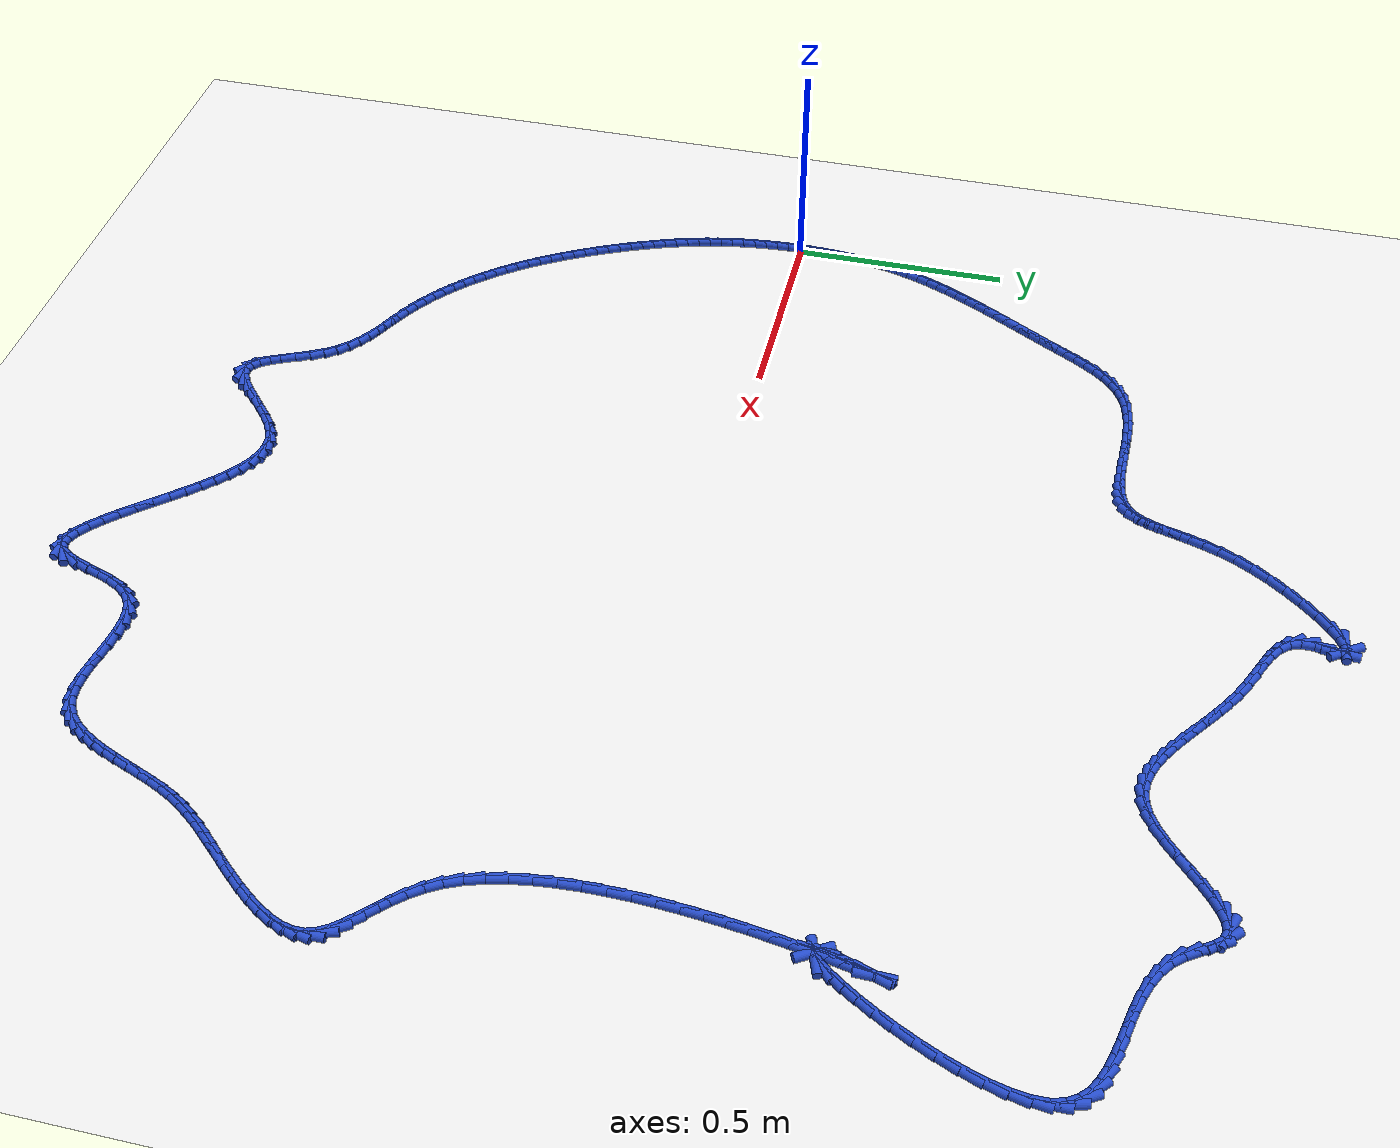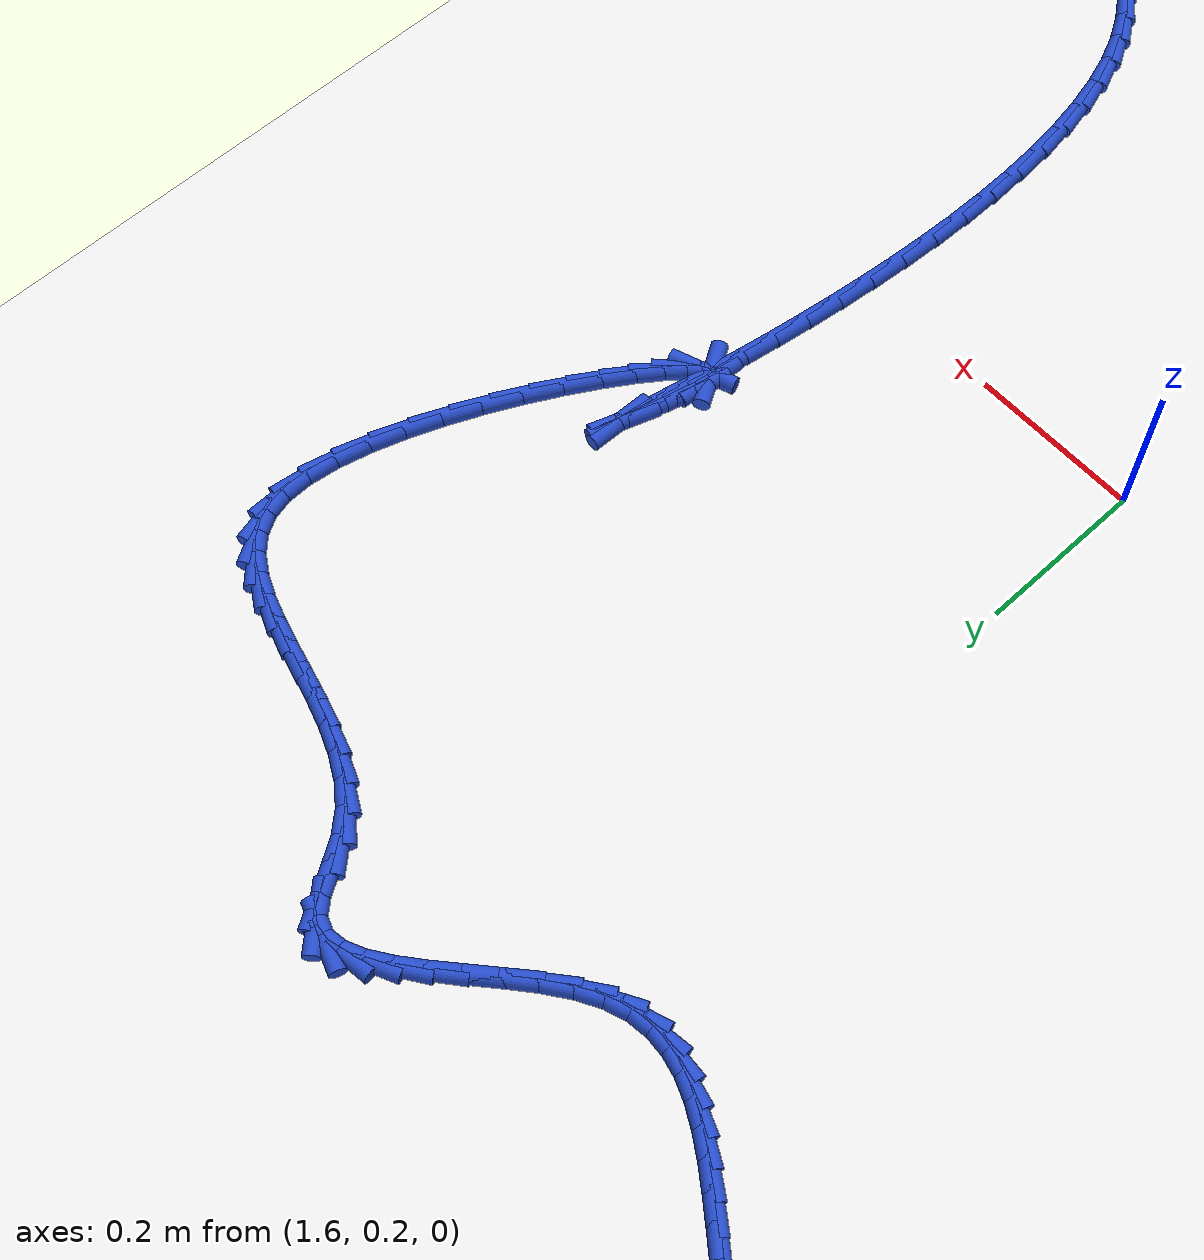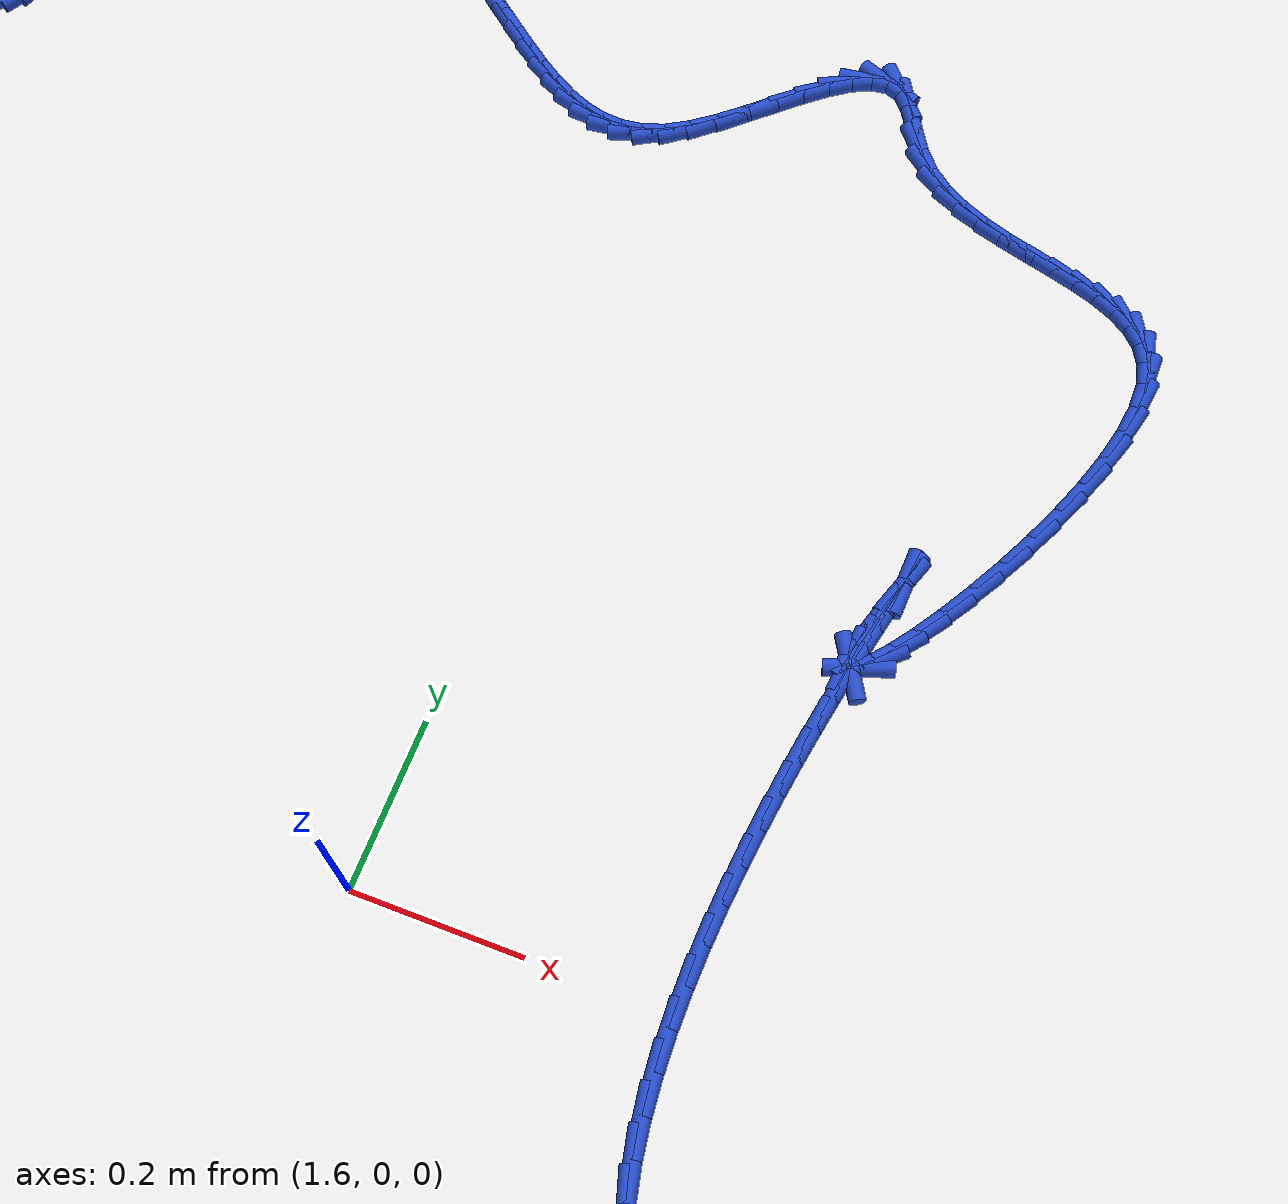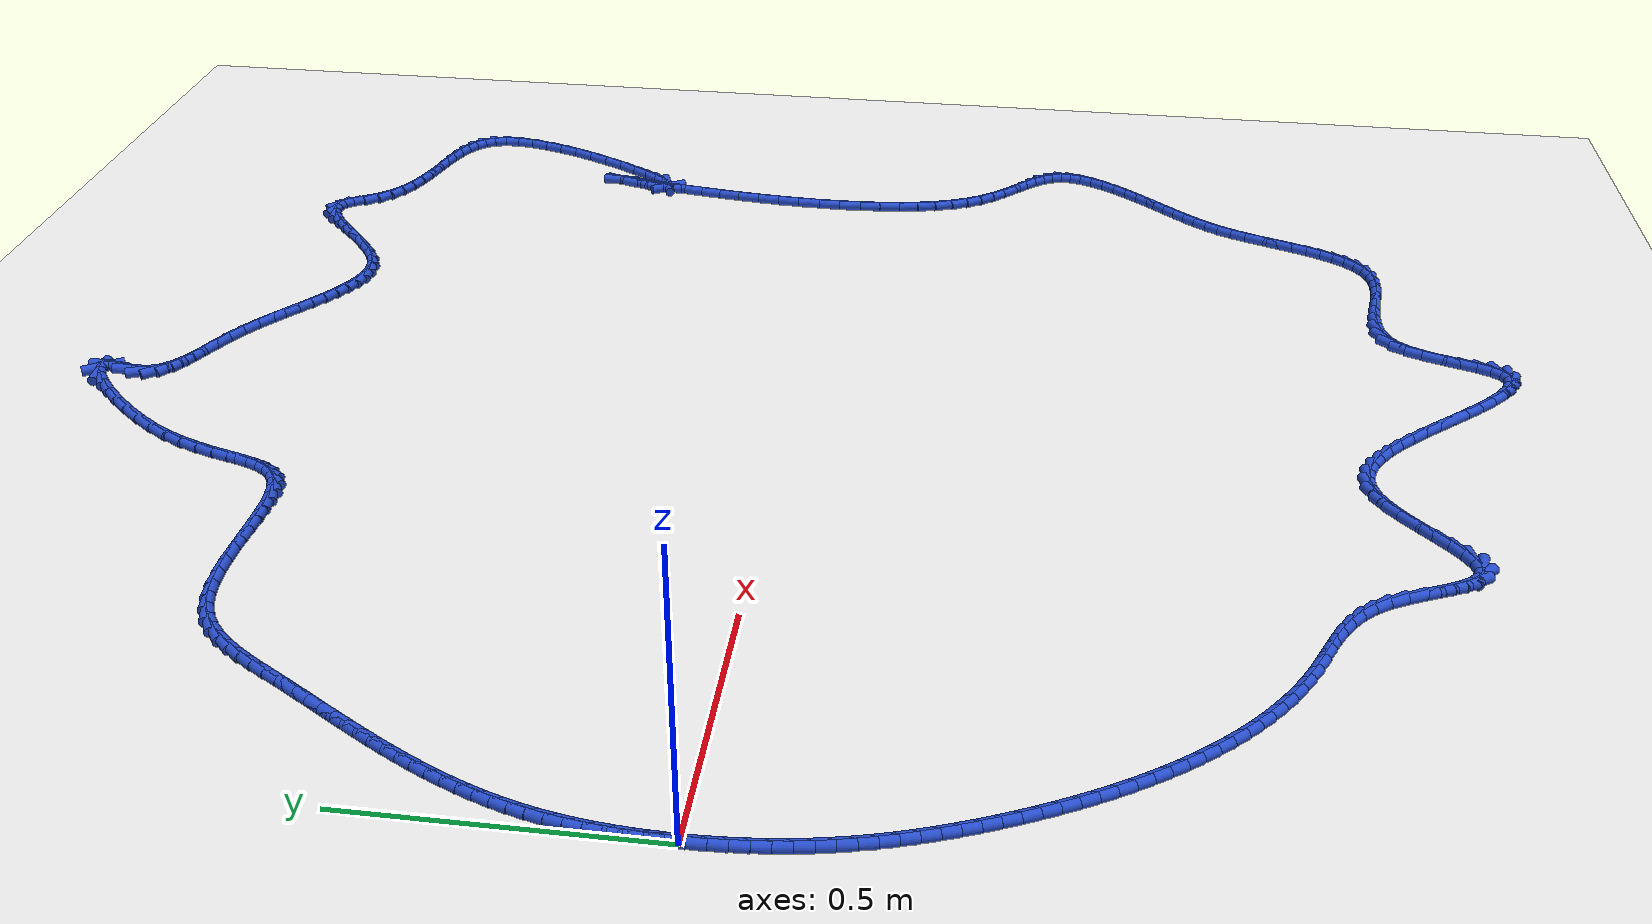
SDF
<sdf version="1.6">
 <world name="default">
  <light name="sun" type="directional">
   <pose>0 0 10 0 -0 0</pose>
   <diffuse>0.8 0.8 0.8 1</diffuse>
   <specular>0.2 0.2 0.2 1</specular>
   <attenuation>
    <range>1000</range>
    <constant>0.9</constant>
    <linear>0.01</linear>
    <quadratic>0.001</quadratic>
   </attenuation>
   <direction>-0.5 0.1 -0.9</direction>
  </light>
  <model name="ground_plane">
   <static>1</static>
   <link name="link">
    <collision name="collision">
     <geometry><plane><normal>0 0 1</normal><size>100 100</size></plane></geometry>
     <surface><friction><ode><mu>100</mu><mu2>50</mu2></ode></friction></surface>
    </collision>
    <visual name="visual">
     <cast_shadows>0</cast_shadows>
     <geometry><plane><normal>0 0 1</normal><size>100 100</size></plane></geometry>
     <material>
      <script><uri>file://media/materials/scripts/gazebo.material</uri><name>Gazebo/WhiteGlow</name></script>
     </material>
    </visual>
   </link>
  </model>
  <gravity>0 0 -9.8</gravity>
  <magnetic_field>6e-06 2.3e-05 -4.2e-05</magnetic_field>
  <atmosphere type="adiabatic"/>
  <physics name="default_physics" default="0" type="ode">
   <max_step_size>0.001</max_step_size>
   <real_time_factor>1</real_time_factor>
   <real_time_update_rate>1000</real_time_update_rate>
  </physics>
  <scene><ambient>0.4 0.4 0.4 1</ambient><background>0.7 0.7 0.7 1</background><shadows>1</shadows></scene>
  <spherical_coordinates>
   <surface_model>EARTH_WGS84</surface_model>
   <latitude_deg>0</latitude_deg>
   <longitude_deg>0</longitude_deg>
   <elevation>0</elevation>
   <heading_deg>0</heading_deg>
  </spherical_coordinates>
  <model name="line">
   <link name="link_0">
    <pose>-6.071532165918825e-18 4.85722573273506e-17 0.01 0 1.57 1.5618496967412394</pose>
    <collision name="collision">
     <geometry><cylinder><radius>0.01</radius><length>0.08</length></cylinder></geometry>
    </collision>
    <visual name="visual">
     <material>
      <script><name>Gazebo/Blue</name><uri>file://media/materials/scripts/gazebo.material</uri></script>
     </material>
     <geometry><cylinder><radius>0.01</radius><length>0.08</length></cylinder></geometry>
    </visual>
   </link>
   <link name="link_1">
    <pose>0.00025737987307691417 0.02876759231284254 0.01 0 1.57 1.534700839534205</pose>
    <collision name="collision">
     <geometry><cylinder><radius>0.01</radius><length>0.08</length></cylinder></geometry>
    </collision>
    <visual name="visual">
     <material>
      <script><name>Gazebo/Blue</name><uri>file://media/materials/scripts/gazebo.material</uri></script>
     </material>
     <geometry><cylinder><radius>0.01</radius><length>0.08</length></cylinder></geometry>
    </visual>
   </link>
   <link name="link_2">
    <pose>0.001295701952245609 0.05752107871654088 0.01 0 1.57 1.5060226653108795</pose>
    <collision name="collision">
     <geometry><cylinder><radius>0.01</radius><length>0.08</length></cylinder></geometry>
    </collision>
    <visual name="visual">
     <material>
      <script><name>Gazebo/Blue</name><uri>file://media/materials/scripts/gazebo.material</uri></script>
     </material>
     <geometry><cylinder><radius>0.01</radius><length>0.08</length></cylinder></geometry>
    </visual>
   </link>
   <link name="link_3">
    <pose>0.003155664080682243 0.08619569926587722 0.01 0 1.57 1.4756687823261825</pose>
    <collision name="collision">
     <geometry><cylinder><radius>0.01</radius><length>0.08</length></cylinder></geometry>
    </collision>
    <visual name="visual">
     <material>
      <script><name>Gazebo/Blue</name><uri>file://media/materials/scripts/gazebo.material</uri></script>
     </material>
     <geometry><cylinder><radius>0.01</radius><length>0.08</length></cylinder></geometry>
    </visual>
   </link>
   <link name="link_4">
    <pose>0.005877964101562978 0.1147266940156338 0.01 0 1.57 1.4434871327278553</pose>
    <collision name="collision">
     <geometry><cylinder><radius>0.01</radius><length>0.08</length></cylinder></geometry>
    </collision>
    <visual name="visual">
     <material>
      <script><name>Gazebo/Blue</name><uri>file://media/materials/scripts/gazebo.material</uri></script>
     </material>
     <geometry><cylinder><radius>0.01</radius><length>0.08</length></cylinder></geometry>
    </visual>
   </link>
   <link name="link_5">
    <pose>0.009503299858063974 0.14304930302059277 0.01 0 1.57 1.4093212751961135</pose>
    <collision name="collision">
     <geometry><cylinder><radius>0.01</radius><length>0.08</length></cylinder></geometry>
    </collision>
    <visual name="visual">
     <material>
      <script><name>Gazebo/Blue</name><uri>file://media/materials/scripts/gazebo.material</uri></script>
     </material>
     <geometry><cylinder><radius>0.01</radius><length>0.08</length></cylinder></geometry>
    </visual>
   </link>
   <link name="link_6">
    <pose>0.0140723691933614 0.17109876633553636 0.01 0 1.57 1.3730125523633765</pose>
    <collision name="collision">
     <geometry><cylinder><radius>0.01</radius><length>0.08</length></cylinder></geometry>
    </collision>
    <visual name="visual">
     <material>
      <script><name>Gazebo/Blue</name><uri>file://media/materials/scripts/gazebo.material</uri></script>
     </material>
     <geometry><cylinder><radius>0.01</radius><length>0.08</length></cylinder></geometry>
    </visual>
   </link>
   <link name="link_7">
    <pose>0.01962586995063141 0.19881032401524673 0.01 0 1.57 1.3344554220983544</pose>
    <collision name="collision">
     <geometry><cylinder><radius>0.01</radius><length>0.08</length></cylinder></geometry>
    </collision>
    <visual name="visual">
     <material>
      <script><name>Gazebo/Blue</name><uri>file://media/materials/scripts/gazebo.material</uri></script>
     </material>
     <geometry><cylinder><radius>0.01</radius><length>0.08</length></cylinder></geometry>
    </visual>
   </link>
   <link name="link_8">
    <pose>0.026203292380306654 0.22612044573771287 0.01 0 1.57 1.2954669962316583</pose>
    <collision name="collision">
     <geometry><cylinder><radius>0.01</radius><length>0.08</length></cylinder></geometry>
    </collision>
    <visual name="visual">
     <material>
      <script><name>Gazebo/Blue</name><uri>file://media/materials/scripts/gazebo.material</uri></script>
     </material>
     <geometry><cylinder><radius>0.01</radius><length>0.08</length></cylinder></geometry>
    </visual>
   </link>
   <link name="link_9">
    <pose>0.03379988727751685 0.2530106477093877 0.01 0 1.57 1.2586226104264027</pose>
    <collision name="collision">
     <geometry><cylinder><radius>0.01</radius><length>0.08</length></cylinder></geometry>
    </collision>
    <visual name="visual">
     <material>
      <script><name>Gazebo/Blue</name><uri>file://media/materials/scripts/gazebo.material</uri></script>
     </material>
     <geometry><cylinder><radius>0.01</radius><length>0.08</length></cylinder></geometry>
    </visual>
   </link>
   <link name="link_10">
    <pose>0.04235495488791489 0.2795194174082357 0.01 0 1.57 1.224285861590087</pose>
    <collision name="collision">
     <geometry><cylinder><radius>0.01</radius><length>0.08</length></cylinder></geometry>
    </collision>
    <visual name="visual">
     <material>
      <script><name>Gazebo/Blue</name><uri>file://media/materials/scripts/gazebo.material</uri></script>
     </material>
     <geometry><cylinder><radius>0.01</radius><length>0.08</length></cylinder></geometry>
    </visual>
   </link>
   <link name="link_11">
    <pose>0.05180420507439614 0.30568889819536876 0.01 0 1.57 1.1926175697821355</pose>
    <collision name="collision">
     <geometry><cylinder><radius>0.01</radius><length>0.08</length></cylinder></geometry>
    </collision>
    <visual name="visual">
     <material>
      <script><name>Gazebo/Blue</name><uri>file://media/materials/scripts/gazebo.material</uri></script>
     </material>
     <geometry><cylinder><radius>0.01</radius><length>0.08</length></cylinder></geometry>
    </visual>
   </link>
   <link name="link_12">
    <pose>0.06208334769985592 0.33156123343189836 0.01 0 1.57 1.1637336648102972</pose>
    <collision name="collision">
     <geometry><cylinder><radius>0.01</radius><length>0.08</length></cylinder></geometry>
    </collision>
    <visual name="visual">
     <material>
      <script><name>Gazebo/Blue</name><uri>file://media/materials/scripts/gazebo.material</uri></script>
     </material>
     <geometry><cylinder><radius>0.01</radius><length>0.08</length></cylinder></geometry>
    </visual>
   </link>
   <link name="link_13">
    <pose>0.07312809262718964 0.35717856647893653 0.01 0 1.57 1.1377100550163985</pose>
    <collision name="collision">
     <geometry><cylinder><radius>0.01</radius><length>0.08</length></cylinder></geometry>
    </collision>
    <visual name="visual">
     <material>
      <script><name>Gazebo/Blue</name><uri>file://media/materials/scripts/gazebo.material</uri></script>
     </material>
     <geometry><cylinder><radius>0.01</radius><length>0.08</length></cylinder></geometry>
    </visual>
   </link>
   <link name="link_14">
    <pose>0.08487414971929266 0.3825830406975948 0.01 0 1.57 1.1145884544039364</pose>
    <collision name="collision">
     <geometry><cylinder><radius>0.01</radius><length>0.08</length></cylinder></geometry>
    </collision>
    <visual name="visual">
     <material>
      <script><name>Gazebo/Blue</name><uri>file://media/materials/scripts/gazebo.material</uri></script>
     </material>
     <geometry><cylinder><radius>0.01</radius><length>0.08</length></cylinder></geometry>
    </visual>
   </link>
   <link name="link_15">
    <pose>0.09725722883906032 0.4078167994489851 0.01 0 1.57 1.09438252692629</pose>
    <collision name="collision">
     <geometry><cylinder><radius>0.01</radius><length>0.08</length></cylinder></geometry>
    </collision>
    <visual name="visual">
     <material>
      <script><name>Gazebo/Blue</name><uri>file://media/materials/scripts/gazebo.material</uri></script>
     </material>
     <geometry><cylinder><radius>0.01</radius><length>0.08</length></cylinder></geometry>
    </visual>
   </link>
   <link name="link_16">
    <pose>0.11021303984938798 0.43292198609421884 0.01 0 1.57 1.0770838513922167</pose>
    <collision name="collision">
     <geometry><cylinder><radius>0.01</radius><length>0.08</length></cylinder></geometry>
    </collision>
    <visual name="visual">
     <material>
      <script><name>Gazebo/Blue</name><uri>file://media/materials/scripts/gazebo.material</uri></script>
     </material>
     <geometry><cylinder><radius>0.01</radius><length>0.08</length></cylinder></geometry>
    </visual>
   </link>
   <link name="link_17">
    <pose>0.12367729261317098 0.45794074399440804 0.01 0 1.57 1.0626673634009953</pose>
    <collision name="collision">
     <geometry><cylinder><radius>0.01</radius><length>0.08</length></cylinder></geometry>
    </collision>
    <visual name="visual">
     <material>
      <script><name>Gazebo/Blue</name><uri>file://media/materials/scripts/gazebo.material</uri></script>
     </material>
     <geometry><cylinder><radius>0.01</radius><length>0.08</length></cylinder></geometry>
    </visual>
   </link>
   <link name="link_18">
    <pose>0.13758569699330478 0.48291521651066444 0.01 0 1.57 1.051096067980115</pose>
    <collision name="collision">
     <geometry><cylinder><radius>0.01</radius><length>0.08</length></cylinder></geometry>
    </collision>
    <visual name="visual">
     <material>
      <script><name>Gazebo/Blue</name><uri>file://media/materials/scripts/gazebo.material</uri></script>
     </material>
     <geometry><cylinder><radius>0.01</radius><length>0.08</length></cylinder></geometry>
    </visual>
   </link>
   <link name="link_19">
    <pose>0.1518739628526846 0.5078875470040995 0.01 0 1.57 1.0423249261464813</pose>
    <collision name="collision">
     <geometry><cylinder><radius>0.01</radius><length>0.08</length></cylinder></geometry>
    </collision>
    <visual name="visual">
     <material>
      <script><name>Gazebo/Blue</name><uri>file://media/materials/scripts/gazebo.material</uri></script>
     </material>
     <geometry><cylinder><radius>0.01</radius><length>0.08</length></cylinder></geometry>
    </visual>
   </link>
   <link name="link_20">
    <pose>0.16647780005420595 0.5328998788358253 0.01 0 1.57 1.0363038976046708</pose>
    <collision name="collision">
     <geometry><cylinder><radius>0.01</radius><length>0.08</length></cylinder></geometry>
    </collision>
    <visual name="visual">
     <material>
      <script><name>Gazebo/Blue</name><uri>file://media/materials/scripts/gazebo.material</uri></script>
     </material>
     <geometry><cylinder><radius>0.01</radius><length>0.08</length></cylinder></geometry>
    </visual>
   </link>
   <link name="link_21">
    <pose>0.1813329184607641 0.5579943553669534 0.01 0 1.57 1.0329801731039916</pose>
    <collision name="collision">
     <geometry><cylinder><radius>0.01</radius><length>0.08</length></cylinder></geometry>
    </collision>
    <visual name="visual">
     <material>
      <script><name>Gazebo/Blue</name><uri>file://media/materials/scripts/gazebo.material</uri></script>
     </material>
     <geometry><cylinder><radius>0.01</radius><length>0.08</length></cylinder></geometry>
    </visual>
   </link>
   <link name="link_22">
    <pose>0.19637502793525435 0.5832131199585954 0.01 0 1.57 1.032299659222334</pose>
    <collision name="collision">
     <geometry><cylinder><radius>0.01</radius><length>0.08</length></cylinder></geometry>
    </collision>
    <visual name="visual">
     <material>
      <script><name>Gazebo/Blue</name><uri>file://media/materials/scripts/gazebo.material</uri></script>
     </material>
     <geometry><cylinder><radius>0.01</radius><length>0.08</length></cylinder></geometry>
    </visual>
   </link>
   <link name="link_23">
    <pose>0.21153983834057216 0.6085983159718632 0.01 0 1.57 1.0342077918414312</pose>
    <collision name="collision">
     <geometry><cylinder><radius>0.01</radius><length>0.08</length></cylinder></geometry>
    </collision>
    <visual name="visual">
     <material>
      <script><name>Gazebo/Blue</name><uri>file://media/materials/scripts/gazebo.material</uri></script>
     </material>
     <geometry><cylinder><radius>0.01</radius><length>0.08</length></cylinder></geometry>
    </visual>
   </link>
   <link name="link_24">
    <pose>0.2267630595396129 0.6341920867678685 0.01 0 1.57 1.0386497581470888</pose>
    <collision name="collision">
     <geometry><cylinder><radius>0.01</radius><length>0.08</length></cylinder></geometry>
    </collision>
    <visual name="visual">
     <material>
      <script><name>Gazebo/Blue</name><uri>file://media/materials/scripts/gazebo.material</uri></script>
     </material>
     <geometry><cylinder><radius>0.01</radius><length>0.08</length></cylinder></geometry>
    </visual>
   </link>
   <link name="link_25">
    <pose>0.241980401395272 0.6600365757077232 0.01 0 1.57 1.0429313332978936</pose>
    <collision name="collision">
     <geometry><cylinder><radius>0.01</radius><length>0.08</length></cylinder></geometry>
    </collision>
    <visual name="visual">
     <material>
      <script><name>Gazebo/Blue</name><uri>file://media/materials/scripts/gazebo.material</uri></script>
     </material>
     <geometry><cylinder><radius>0.01</radius><length>0.08</length></cylinder></geometry>
    </visual>
   </link>
   <link name="link_26">
    <pose>0.25717833736589857 0.686102722968214 0.01 0 1.57 1.0322560216911314</pose>
    <collision name="collision">
     <geometry><cylinder><radius>0.01</radius><length>0.08</length></cylinder></geometry>
    </collision>
    <visual name="visual">
     <material>
      <script><name>Gazebo/Blue</name><uri>file://media/materials/scripts/gazebo.material</uri></script>
     </material>
     <geometry><cylinder><radius>0.01</radius><length>0.08</length></cylinder></geometry>
    </visual>
   </link>
   <link name="link_27">
    <pose>0.2726280027185645 0.7119621899308509 0.01 0 1.57 1.0010008215164532</pose>
    <collision name="collision">
     <geometry><cylinder><radius>0.01</radius><length>0.08</length></cylinder></geometry>
    </collision>
    <visual name="visual">
     <material>
      <script><name>Gazebo/Blue</name><uri>file://media/materials/scripts/gazebo.material</uri></script>
     </material>
     <geometry><cylinder><radius>0.01</radius><length>0.08</length></cylinder></geometry>
    </visual>
   </link>
   <link name="link_28">
    <pose>0.2886996936329558 0.7370475506513653 0.01 0 1.57 0.9476431186268373</pose>
    <collision name="collision">
     <geometry><cylinder><radius>0.01</radius><length>0.08</length></cylinder></geometry>
    </collision>
    <visual name="visual">
     <material>
      <script><name>Gazebo/Blue</name><uri>file://media/materials/scripts/gazebo.material</uri></script>
     </material>
     <geometry><cylinder><radius>0.01</radius><length>0.08</length></cylinder></geometry>
    </visual>
   </link>
   <link name="link_29">
    <pose>0.30576380753950977 0.7607912371668636 0.01 0 1.57 0.869831654823619</pose>
    <collision name="collision">
     <geometry><cylinder><radius>0.01</radius><length>0.08</length></cylinder></geometry>
    </collision>
    <visual name="visual">
     <material>
      <script><name>Gazebo/Blue</name><uri>file://media/materials/scripts/gazebo.material</uri></script>
     </material>
     <geometry><cylinder><radius>0.01</radius><length>0.08</length></cylinder></geometry>
    </visual>
   </link>
   <link name="link_30">
    <pose>0.32419074186866415 0.7826256815144527 0.01 0 1.57 0.7650931882227393</pose>
    <collision name="collision">
     <geometry><cylinder><radius>0.01</radius><length>0.08</length></cylinder></geometry>
    </collision>
    <visual name="visual">
     <material>
      <script><name>Gazebo/Blue</name><uri>file://media/materials/scripts/gazebo.material</uri></script>
     </material>
     <geometry><cylinder><radius>0.01</radius><length>0.08</length></cylinder></geometry>
    </visual>
   </link>
   <link name="link_31">
    <pose>0.3443508940508568 0.8019833157312395 0.01 0 1.57 0.6323542122007462</pose>
    <collision name="collision">
     <geometry><cylinder><radius>0.01</radius><length>0.08</length></cylinder></geometry>
    </collision>
    <visual name="visual">
     <material>
      <script><name>Gazebo/Blue</name><uri>file://media/materials/scripts/gazebo.material</uri></script>
     </material>
     <geometry><cylinder><radius>0.01</radius><length>0.08</length></cylinder></geometry>
    </visual>
   </link>
   <link name="link_32">
    <pose>0.3666146615165252 0.8182965718543307 0.01 0 1.57 0.474643444710666</pose>
    <collision name="collision">
     <geometry><cylinder><radius>0.01</radius><length>0.08</length></cylinder></geometry>
    </collision>
    <visual name="visual">
     <material>
      <script><name>Gazebo/Blue</name><uri>file://media/materials/scripts/gazebo.material</uri></script>
     </material>
     <geometry><cylinder><radius>0.01</radius><length>0.08</length></cylinder></geometry>
    </visual>
   </link>
   <link name="link_33">
    <pose>0.3913472668551906 0.831004712277912 0.01 0 1.57 0.31815705306391706</pose>
    <collision name="collision">
     <geometry><cylinder><radius>0.01</radius><length>0.08</length></cylinder></geometry>
    </collision>
    <visual name="visual">
     <material>
      <script><name>Gazebo/Blue</name><uri>file://media/materials/scripts/gazebo.material</uri></script>
     </material>
     <geometry><cylinder><radius>0.01</radius><length>0.08</length></cylinder></geometry>
    </visual>
   </link>
   <link name="link_34">
    <pose>0.41858853548119207 0.8399764964443867 0.01 0 1.57 0.19496888457943615</pose>
    <collision name="collision">
     <geometry><cylinder><radius>0.01</radius><length>0.08</length></cylinder></geometry>
    </collision>
    <visual name="visual">
     <material>
      <script><name>Gazebo/Blue</name><uri>file://media/materials/scripts/gazebo.material</uri></script>
     </material>
     <geometry><cylinder><radius>0.01</radius><length>0.08</length></cylinder></geometry>
    </visual>
   </link>
   <link name="link_35">
    <pose>0.4478651638119439 0.8457579711432657 0.01 0 1.57 0.10344504276795878</pose>
    <collision name="collision">
     <geometry><cylinder><radius>0.01</radius><length>0.08</length></cylinder></geometry>
    </collision>
    <visual name="visual">
     <material>
      <script><name>Gazebo/Blue</name><uri>file://media/materials/scripts/gazebo.material</uri></script>
     </material>
     <geometry><cylinder><radius>0.01</radius><length>0.08</length></cylinder></geometry>
    </visual>
   </link>
   <link name="link_36">
    <pose>0.4786586677678103 0.8489548176403252 0.01 0 1.57 0.038289768305461734</pose>
    <collision name="collision">
     <geometry><cylinder><radius>0.01</radius><length>0.08</length></cylinder></geometry>
    </collision>
    <visual name="visual">
     <material>
      <script><name>Gazebo/Blue</name><uri>file://media/materials/scripts/gazebo.material</uri></script>
     </material>
     <geometry><cylinder><radius>0.01</radius><length>0.08</length></cylinder></geometry>
    </visual>
   </link>
   <link name="link_37">
    <pose>0.5104505632691555 0.8501727172013416 0.01 0 1.57 -0.004814261821521192</pose>
    <collision name="collision">
     <geometry><cylinder><radius>0.01</radius><length>0.08</length></cylinder></geometry>
    </collision>
    <visual name="visual">
     <material>
      <script><name>Gazebo/Blue</name><uri>file://media/materials/scripts/gazebo.material</uri></script>
     </material>
     <geometry><cylinder><radius>0.01</radius><length>0.08</length></cylinder></geometry>
    </visual>
   </link>
   <link name="link_38">
    <pose>0.5427223662363431 0.8500173510920903 0.01 0 1.57 -0.028625691763009557</pose>
    <collision name="collision">
     <geometry><cylinder><radius>0.01</radius><length>0.08</length></cylinder></geometry>
    </collision>
    <visual name="visual">
     <material>
      <script><name>Gazebo/Blue</name><uri>file://media/materials/scripts/gazebo.material</uri></script>
     </material>
     <geometry><cylinder><radius>0.01</radius><length>0.08</length></cylinder></geometry>
    </visual>
   </link>
   <link name="link_39">
    <pose>0.5749555925897378 0.8490944005783476 0.01 0 1.57 -0.034234881993086184</pose>
    <collision name="collision">
     <geometry><cylinder><radius>0.01</radius><length>0.08</length></cylinder></geometry>
    </collision>
    <visual name="visual">
     <material>
      <script><name>Gazebo/Blue</name><uri>file://media/materials/scripts/gazebo.material</uri></script>
     </material>
     <geometry><cylinder><radius>0.01</radius><length>0.08</length></cylinder></geometry>
    </visual>
   </link>
   <link name="link_40">
    <pose>0.6066317582497033 0.8480095469258895 0.01 0 1.57 -0.020946691400877338</pose>
    <collision name="collision">
     <geometry><cylinder><radius>0.01</radius><length>0.08</length></cylinder></geometry>
    </collision>
    <visual name="visual">
     <material>
      <script><name>Gazebo/Blue</name><uri>file://media/materials/scripts/gazebo.material</uri></script>
     </material>
     <geometry><cylinder><radius>0.01</radius><length>0.08</length></cylinder></geometry>
    </visual>
   </link>
   <link name="link_41">
    <pose>0.6372323791366038 0.8473684714004919 0.01 0 1.57 0.014078071878091328</pose>
    <collision name="collision">
     <geometry><cylinder><radius>0.01</radius><length>0.08</length></cylinder></geometry>
    </collision>
    <visual name="visual">
     <material>
      <script><name>Gazebo/Blue</name><uri>file://media/materials/scripts/gazebo.material</uri></script>
     </material>
     <geometry><cylinder><radius>0.01</radius><length>0.08</length></cylinder></geometry>
    </visual>
   </link>
   <link name="link_42">
    <pose>0.6662389711708036 0.8477768552679308 0.01 0 1.57 0.07657779723410559</pose>
    <collision name="collision">
     <geometry><cylinder><radius>0.01</radius><length>0.08</length></cylinder></geometry>
    </collision>
    <visual name="visual">
     <material>
      <script><name>Gazebo/Blue</name><uri>file://media/materials/scripts/gazebo.material</uri></script>
     </material>
     <geometry><cylinder><radius>0.01</radius><length>0.08</length></cylinder></geometry>
    </visual>
   </link>
   <link name="link_43">
    <pose>0.6931330502726664 0.8498403797939824 0.01 0 1.57 0.17637545547229563</pose>
    <collision name="collision">
     <geometry><cylinder><radius>0.01</radius><length>0.08</length></cylinder></geometry>
    </collision>
    <visual name="visual">
     <material>
      <script><name>Gazebo/Blue</name><uri>file://media/materials/scripts/gazebo.material</uri></script>
     </material>
     <geometry><cylinder><radius>0.01</radius><length>0.08</length></cylinder></geometry>
    </visual>
   </link>
   <link name="link_44">
    <pose>0.7173961323625564 0.8541647262444225 0.01 0 1.57 0.32825744072564345</pose>
    <collision name="collision">
     <geometry><cylinder><radius>0.01</radius><length>0.08</length></cylinder></geometry>
    </collision>
    <visual name="visual">
     <material>
      <script><name>Gazebo/Blue</name><uri>file://media/materials/scripts/gazebo.material</uri></script>
     </material>
     <geometry><cylinder><radius>0.01</radius><length>0.08</length></cylinder></geometry>
    </visual>
   </link>
   <link name="link_45">
    <pose>0.7385097333608381 0.8613555758850274 0.01 0 1.57 0.5480415390426403</pose>
    <collision name="collision">
     <geometry><cylinder><radius>0.01</radius><length>0.08</length></cylinder></geometry>
    </collision>
    <visual name="visual">
     <material>
      <script><name>Gazebo/Blue</name><uri>file://media/materials/scripts/gazebo.material</uri></script>
     </material>
     <geometry><cylinder><radius>0.01</radius><length>0.08</length></cylinder></geometry>
    </visual>
   </link>
   <link name="link_46">
    <pose>0.7559666330440499 0.8720115083398305 0.01 0 1.57 0.8045073944918965</pose>
    <collision name="collision">
     <geometry><cylinder><radius>0.01</radius><length>0.08</length></cylinder></geometry>
    </collision>
    <visual name="visual">
     <material>
      <script><name>Gazebo/Blue</name><uri>file://media/materials/scripts/gazebo.material</uri></script>
     </material>
     <geometry><cylinder><radius>0.01</radius><length>0.08</length></cylinder></geometry>
    </visual>
   </link>
   <link name="link_47">
    <pose>0.7698038735795254 0.886387956405233 0.01 0 1.57 1.0176272706725502</pose>
    <collision name="collision">
     <geometry><cylinder><radius>0.01</radius><length>0.08</length></cylinder></geometry>
    </collision>
    <visual name="visual">
     <material>
      <script><name>Gazebo/Blue</name><uri>file://media/materials/scripts/gazebo.material</uri></script>
     </material>
     <geometry><cylinder><radius>0.01</radius><length>0.08</length></cylinder></geometry>
    </visual>
   </link>
   <link name="link_48">
    <pose>0.7808340677343297 0.9042513707333547 0.01 0 1.57 1.163459142255062</pose>
    <collision name="collision">
     <geometry><cylinder><radius>0.01</radius><length>0.08</length></cylinder></geometry>
    </collision>
    <visual name="visual">
     <material>
      <script><name>Gazebo/Blue</name><uri>file://media/materials/scripts/gazebo.material</uri></script>
     </material>
     <geometry><cylinder><radius>0.01</radius><length>0.08</length></cylinder></geometry>
    </visual>
   </link>
   <link name="link_49">
    <pose>0.7899291805404246 0.9253307815303004 0.01 0 1.57 1.2481525484894271</pose>
    <collision name="collision">
     <geometry><cylinder><radius>0.01</radius><length>0.08</length></cylinder></geometry>
    </collision>
    <visual name="visual">
     <material>
      <script><name>Gazebo/Blue</name><uri>file://media/materials/scripts/gazebo.material</uri></script>
     </material>
     <geometry><cylinder><radius>0.01</radius><length>0.08</length></cylinder></geometry>
    </visual>
   </link>
   <link name="link_50">
    <pose>0.7979611770297719 0.949355219002175 0.01 0 1.57 1.2851466532019082</pose>
    <collision name="collision">
     <geometry><cylinder><radius>0.01</radius><length>0.08</length></cylinder></geometry>
    </collision>
    <visual name="visual">
     <material>
      <script><name>Gazebo/Blue</name><uri>file://media/materials/scripts/gazebo.material</uri></script>
     </material>
     <geometry><cylinder><radius>0.01</radius><length>0.08</length></cylinder></geometry>
    </visual>
   </link>
   <link name="link_51">
    <pose>0.8058020222343341 0.9760537133550845 0.01 0 1.57 1.285935398453922</pose>
    <collision name="collision">
     <geometry><cylinder><radius>0.01</radius><length>0.08</length></cylinder></geometry>
    </collision>
    <visual name="visual">
     <material>
      <script><name>Gazebo/Blue</name><uri>file://media/materials/scripts/gazebo.material</uri></script>
     </material>
     <geometry><cylinder><radius>0.01</radius><length>0.08</length></cylinder></geometry>
    </visual>
   </link>
   <link name="link_52">
    <pose>0.8143236811860728 1.0051552947951337 0.01 0 1.57 1.2587817243880264</pose>
    <collision name="collision">
     <geometry><cylinder><radius>0.01</radius><length>0.08</length></cylinder></geometry>
    </collision>
    <visual name="visual">
     <material>
      <script><name>Gazebo/Blue</name><uri>file://media/materials/scripts/gazebo.material</uri></script>
     </material>
     <geometry><cylinder><radius>0.01</radius><length>0.08</length></cylinder></geometry>
    </visual>
   </link>
   <link name="link_53">
    <pose>0.82439811891695 1.0363889935284278 0.01 0 1.57 1.2096802552737174</pose>
    <collision name="collision">
     <geometry><cylinder><radius>0.01</radius><length>0.08</length></cylinder></geometry>
    </collision>
    <visual name="visual">
     <material>
      <script><name>Gazebo/Blue</name><uri>file://media/materials/scripts/gazebo.material</uri></script>
     </material>
     <geometry><cylinder><radius>0.01</radius><length>0.08</length></cylinder></geometry>
    </visual>
   </link>
   <link name="link_54">
    <pose>0.836897300458928 1.0694838397610718 0.01 0 1.57 1.1434529510312286</pose>
    <collision name="collision">
     <geometry><cylinder><radius>0.01</radius><length>0.08</length></cylinder></geometry>
    </collision>
    <visual name="visual">
     <material>
      <script><name>Gazebo/Blue</name><uri>file://media/materials/scripts/gazebo.material</uri></script>
     </material>
     <geometry><cylinder><radius>0.01</radius><length>0.08</length></cylinder></geometry>
    </visual>
   </link>
   <link name="link_55">
    <pose>0.8526931908439687 1.1041688636991716 0.01 0 1.57 1.0646016290601974</pose>
    <collision name="collision">
     <geometry><cylinder><radius>0.01</radius><length>0.08</length></cylinder></geometry>
    </collision>
    <visual name="visual">
     <material>
      <script><name>Gazebo/Blue</name><uri>file://media/materials/scripts/gazebo.material</uri></script>
     </material>
     <geometry><cylinder><radius>0.01</radius><length>0.08</length></cylinder></geometry>
    </visual>
   </link>
   <link name="link_56">
    <pose>0.8726511241609208 1.1401697499167087 0.01 0 1.57 0.9867419532965794</pose>
    <collision name="collision">
     <geometry><cylinder><radius>0.01</radius><length>0.08</length></cylinder></geometry>
    </collision>
    <visual name="visual">
     <material>
      <script><name>Gazebo/Blue</name><uri>file://media/materials/scripts/gazebo.material</uri></script>
     </material>
     <geometry><cylinder><radius>0.01</radius><length>0.08</length></cylinder></geometry>
    </visual>
   </link>
   <link name="link_57">
    <pose>0.8968846697390839 1.176832881237407 0.01 0 1.57 0.9232519375012668</pose>
    <collision name="collision">
     <geometry><cylinder><radius>0.01</radius><length>0.08</length></cylinder></geometry>
    </collision>
    <visual name="visual">
     <material>
      <script><name>Gazebo/Blue</name><uri>file://media/materials/scripts/gazebo.material</uri></script>
     </material>
     <geometry><cylinder><radius>0.01</radius><length>0.08</length></cylinder></geometry>
    </visual>
   </link>
   <link name="link_58">
    <pose>0.9240738010889508 1.2127813219251233 0.01 0 1.57 0.8670865732290968</pose>
    <collision name="collision">
     <geometry><cylinder><radius>0.01</radius><length>0.08</length></cylinder></geometry>
    </collision>
    <visual name="visual">
     <material>
      <script><name>Gazebo/Blue</name><uri>file://media/materials/scripts/gazebo.material</uri></script>
     </material>
     <geometry><cylinder><radius>0.01</radius><length>0.08</length></cylinder></geometry>
    </visual>
   </link>
   <link name="link_59">
    <pose>0.9527374121513218 1.2465568637952003 0.01 0 1.57 0.8106889304128033</pose>
    <collision name="collision">
     <geometry><cylinder><radius>0.01</radius><length>0.08</length></cylinder></geometry>
    </collision>
    <visual name="visual">
     <material>
      <script><name>Gazebo/Blue</name><uri>file://media/materials/scripts/gazebo.material</uri></script>
     </material>
     <geometry><cylinder><radius>0.01</radius><length>0.08</length></cylinder></geometry>
    </visual>
   </link>
   <link name="link_60">
    <pose>0.9813943968669966 1.276701298662981 0.01 0 1.57 0.7449385307859171</pose>
    <collision name="collision">
     <geometry><cylinder><radius>0.01</radius><length>0.08</length></cylinder></geometry>
    </collision>
    <visual name="visual">
     <material>
      <script><name>Gazebo/Blue</name><uri>file://media/materials/scripts/gazebo.material</uri></script>
     </material>
     <geometry><cylinder><radius>0.01</radius><length>0.08</length></cylinder></geometry>
    </visual>
   </link>
   <link name="link_61">
    <pose>1.0085636491767742 1.3017564183438077 0.01 0 1.57 0.6528830683168945</pose>
    <collision name="collision">
     <geometry><cylinder><radius>0.01</radius><length>0.08</length></cylinder></geometry>
    </collision>
    <visual name="visual">
     <material>
      <script><name>Gazebo/Blue</name><uri>file://media/materials/scripts/gazebo.material</uri></script>
     </material>
     <geometry><cylinder><radius>0.01</radius><length>0.08</length></cylinder></geometry>
    </visual>
   </link>
   <link name="link_62">
    <pose>1.032764063021455 1.3202640146530222 0.01 0 1.57 0.4887061611051287</pose>
    <collision name="collision">
     <geometry><cylinder><radius>0.01</radius><length>0.08</length></cylinder></geometry>
    </collision>
    <visual name="visual">
     <material>
      <script><name>Gazebo/Blue</name><uri>file://media/materials/scripts/gazebo.material</uri></script>
     </material>
     <geometry><cylinder><radius>0.01</radius><length>0.08</length></cylinder></geometry>
    </visual>
   </link>
   <link name="link_63">
    <pose>1.0525145323418381 1.3307658794059671 0.01 0 1.57 0.07496552367978968</pose>
    <collision name="collision">
     <geometry><cylinder><radius>0.01</radius><length>0.08</length></cylinder></geometry>
    </collision>
    <visual name="visual">
     <material>
      <script><name>Gazebo/Blue</name><uri>file://media/materials/scripts/gazebo.material</uri></script>
     </material>
     <geometry><cylinder><radius>0.01</radius><length>0.08</length></cylinder></geometry>
    </visual>
   </link>
   <link name="link_64">
    <pose>1.066333951078723 1.3318038044179852 0.01 0 1.57 -0.9956655265323965</pose>
    <collision name="collision">
     <geometry><cylinder><radius>0.01</radius><length>0.08</length></cylinder></geometry>
    </collision>
    <visual name="visual">
     <material>
      <script><name>Gazebo/Blue</name><uri>file://media/materials/scripts/gazebo.material</uri></script>
     </material>
     <geometry><cylinder><radius>0.01</radius><length>0.08</length></cylinder></geometry>
    </visual>
   </link>
   <link name="link_65">
    <pose>1.0727412131729093 1.3219195815044185 0.01 0 1.57 1.4744912303399906</pose>
    <collision name="collision">
     <geometry><cylinder><radius>0.01</radius><length>0.08</length></cylinder></geometry>
    </collision>
    <visual name="visual">
     <material>
      <script><name>Gazebo/Blue</name><uri>file://media/materials/scripts/gazebo.material</uri></script>
     </material>
     <geometry><cylinder><radius>0.01</radius><length>0.08</length></cylinder></geometry>
    </visual>
   </link>
   <link name="link_66">
    <pose>1.070623663172188 1.2999996676046883 0.01 0 1.57 1.3758665254964286</pose>
    <collision name="collision">
     <geometry><cylinder><radius>0.01</radius><length>0.08</length></cylinder></geometry>
    </collision>
    <visual name="visual">
     <material>
      <script><name>Gazebo/Blue</name><uri>file://media/materials/scripts/gazebo.material</uri></script>
     </material>
     <geometry><cylinder><radius>0.01</radius><length>0.08</length></cylinder></geometry>
    </visual>
   </link>
   <link name="link_67">
    <pose>1.06479409993601 1.2704734537905 0.01 0 1.57 1.5645068673455942</pose>
    <collision name="collision">
     <geometry><cylinder><radius>0.01</radius><length>0.08</length></cylinder></geometry>
    </collision>
    <visual name="visual">
     <material>
      <script><name>Gazebo/Blue</name><uri>file://media/materials/scripts/gazebo.material</uri></script>
     </material>
     <geometry><cylinder><radius>0.01</radius><length>0.08</length></cylinder></geometry>
    </visual>
   </link>
   <link name="link_68">
    <pose>1.0646152558782902 1.242038307501844 0.01 0 1.57 -1.185910926088481</pose>
    <collision name="collision">
     <geometry><cylinder><radius>0.01</radius><length>0.08</length></cylinder></geometry>
    </collision>
    <visual name="visual">
     <material>
      <script><name>Gazebo/Blue</name><uri>file://media/materials/scripts/gazebo.material</uri></script>
     </material>
     <geometry><cylinder><radius>0.01</radius><length>0.08</length></cylinder></geometry>
    </visual>
   </link>
   <link name="link_69">
    <pose>1.074087779421236 1.218654476815771 0.01 0 1.57 -0.8337503875959589</pose>
    <collision name="collision">
     <geometry><cylinder><radius>0.01</radius><length>0.08</length></cylinder></geometry>
    </collision>
    <visual name="visual">
     <material>
      <script><name>Gazebo/Blue</name><uri>file://media/materials/scripts/gazebo.material</uri></script>
     </material>
     <geometry><cylinder><radius>0.01</radius><length>0.08</length></cylinder></geometry>
    </visual>
   </link>
   <link name="link_70">
    <pose>1.0916223834838321 1.1993365825338809 0.01 0 1.57 -0.6058743552661893</pose>
    <collision name="collision">
     <geometry><cylinder><radius>0.01</radius><length>0.08</length></cylinder></geometry>
    </collision>
    <visual name="visual">
     <material>
      <script><name>Gazebo/Blue</name><uri>file://media/materials/scripts/gazebo.material</uri></script>
     </material>
     <geometry><cylinder><radius>0.01</radius><length>0.08</length></cylinder></geometry>
    </visual>
   </link>
   <link name="link_71">
    <pose>1.115379466020502 1.1828777823450989 0.01 0 1.57 -0.4843678262053638</pose>
    <collision name="collision">
     <geometry><cylinder><radius>0.01</radius><length>0.08</length></cylinder></geometry>
    </collision>
    <visual name="visual">
     <material>
      <script><name>Gazebo/Blue</name><uri>file://media/materials/scripts/gazebo.material</uri></script>
     </material>
     <geometry><cylinder><radius>0.01</radius><length>0.08</length></cylinder></geometry>
    </visual>
   </link>
   <link name="link_72">
    <pose>1.1435194249856704 1.1680712339383525 0.01 0 1.57 -0.43775853810819215</pose>
    <collision name="collision">
     <geometry><cylinder><radius>0.01</radius><length>0.08</length></cylinder></geometry>
    </collision>
    <visual name="visual">
     <material>
      <script><name>Gazebo/Blue</name><uri>file://media/materials/scripts/gazebo.material</uri></script>
     </material>
     <geometry><cylinder><radius>0.01</radius><length>0.08</length></cylinder></geometry>
    </visual>
   </link>
   <link name="link_73">
    <pose>1.17420265833376 1.1537100950025676 0.01 0 1.57 -0.4489912112018849</pose>
    <collision name="collision">
     <geometry><cylinder><radius>0.01</radius><length>0.08</length></cylinder></geometry>
    </collision>
    <visual name="visual">
     <material>
      <script><name>Gazebo/Blue</name><uri>file://media/materials/scripts/gazebo.material</uri></script>
     </material>
     <geometry><cylinder><radius>0.01</radius><length>0.08</length></cylinder></geometry>
    </visual>
   </link>
   <link name="link_74">
    <pose>1.205589564019194 1.1385875232266707 0.01 0 1.57 -0.5074245883647727</pose>
    <collision name="collision">
     <geometry><cylinder><radius>0.01</radius><length>0.08</length></cylinder></geometry>
    </collision>
    <visual name="visual">
     <material>
      <script><name>Gazebo/Blue</name><uri>file://media/materials/scripts/gazebo.material</uri></script>
     </material>
     <geometry><cylinder><radius>0.01</radius><length>0.08</length></cylinder></geometry>
    </visual>
   </link>
   <link name="link_75">
    <pose>1.2360261260319716 1.1216653316465894 0.01 0 1.57 -0.5685375864182829</pose>
    <collision name="collision">
     <geometry><cylinder><radius>0.01</radius><length>0.08</length></cylinder></geometry>
    </collision>
    <visual name="visual">
     <material>
      <script><name>Gazebo/Blue</name><uri>file://media/materials/scripts/gazebo.material</uri></script>
     </material>
     <geometry><cylinder><radius>0.01</radius><length>0.08</length></cylinder></geometry>
    </visual>
   </link>
   <link name="link_76">
    <pose>1.2651362435472981 1.1030666665221327 0.01 0 1.57 -0.6131494041517901</pose>
    <collision name="collision">
     <geometry><cylinder><radius>0.01</radius><length>0.08</length></cylinder></geometry>
    </collision>
    <visual name="visual">
     <material>
      <script><name>Gazebo/Blue</name><uri>file://media/materials/scripts/gazebo.material</uri></script>
     </material>
     <geometry><cylinder><radius>0.01</radius><length>0.08</length></cylinder></geometry>
    </visual>
   </link>
   <link name="link_77">
    <pose>1.2930818725664321 1.0834036449584812 0.01 0 1.57 -0.6412366648807184</pose>
    <collision name="collision">
     <geometry><cylinder><radius>0.01</radius><length>0.08</length></cylinder></geometry>
    </collision>
    <visual name="visual">
     <material>
      <script><name>Gazebo/Blue</name><uri>file://media/materials/scripts/gazebo.material</uri></script>
     </material>
     <geometry><cylinder><radius>0.01</radius><length>0.08</length></cylinder></geometry>
    </visual>
   </link>
   <link name="link_78">
    <pose>1.3200268461189721 1.0632900898511553 0.01 0 1.57 -0.6524890521754039</pose>
    <collision name="collision">
     <geometry><cylinder><radius>0.01</radius><length>0.08</length></cylinder></geometry>
    </collision>
    <visual name="visual">
     <material>
      <script><name>Gazebo/Blue</name><uri>file://media/materials/scripts/gazebo.material</uri></script>
     </material>
     <geometry><cylinder><radius>0.01</radius><length>0.08</length></cylinder></geometry>
    </visual>
   </link>
   <link name="link_79">
    <pose>1.3461349972345178 1.043339824095674 0.01 0 1.57 -0.6459319004834038</pose>
    <collision name="collision">
     <geometry><cylinder><radius>0.01</radius><length>0.08</length></cylinder></geometry>
    </collision>
    <visual name="visual">
     <material>
      <script><name>Gazebo/Blue</name><uri>file://media/materials/scripts/gazebo.material</uri></script>
     </material>
     <geometry><cylinder><radius>0.01</radius><length>0.08</length></cylinder></geometry>
    </visual>
   </link>
   <link name="link_80">
    <pose>1.371570158942668 1.0241666705875578 0.01 0 1.57 -0.6196629176166212</pose>
    <collision name="collision">
     <geometry><cylinder><radius>0.01</radius><length>0.08</length></cylinder></geometry>
    </collision>
    <visual name="visual">
     <material>
      <script><name>Gazebo/Blue</name><uri>file://media/materials/scripts/gazebo.material</uri></script>
     </material>
     <geometry><cylinder><radius>0.01</radius><length>0.08</length></cylinder></geometry>
    </visual>
   </link>
   <link name="link_81">
    <pose>1.3964961642730223 1.0063844522223258 0.01 0 1.57 -0.5706345906195713</pose>
    <collision name="collision">
     <geometry><cylinder><radius>0.01</radius><length>0.08</length></cylinder></geometry>
    </collision>
    <visual name="visual">
     <material>
      <script><name>Gazebo/Blue</name><uri>file://media/materials/scripts/gazebo.material</uri></script>
     </material>
     <geometry><cylinder><radius>0.01</radius><length>0.08</length></cylinder></geometry>
    </visual>
   </link>
   <link name="link_82">
    <pose>1.4210768462551797 0.9906069918954976 0.01 0 1.57 -0.4946036932100912</pose>
    <collision name="collision">
     <geometry><cylinder><radius>0.01</radius><length>0.08</length></cylinder></geometry>
    </collision>
    <visual name="visual">
     <material>
      <script><name>Gazebo/Blue</name><uri>file://media/materials/scripts/gazebo.material</uri></script>
     </material>
     <geometry><cylinder><radius>0.01</radius><length>0.08</length></cylinder></geometry>
    </visual>
   </link>
   <link name="link_83">
    <pose>1.445476037918739 0.9774481125025931 0.01 0 1.57 -0.3866385325265861</pose>
    <collision name="collision">
     <geometry><cylinder><radius>0.01</radius><length>0.08</length></cylinder></geometry>
    </collision>
    <visual name="visual">
     <material>
      <script><name>Gazebo/Blue</name><uri>file://media/materials/scripts/gazebo.material</uri></script>
     </material>
     <geometry><cylinder><radius>0.01</radius><length>0.08</length></cylinder></geometry>
    </visual>
   </link>
   <link name="link_84">
    <pose>1.4698575722933 0.967521636939132 0.01 0 1.57 -0.24299466918522217</pose>
    <collision name="collision">
     <geometry><cylinder><radius>0.01</radius><length>0.08</length></cylinder></geometry>
    </collision>
    <visual name="visual">
     <material>
      <script><name>Gazebo/Blue</name><uri>file://media/materials/scripts/gazebo.material</uri></script>
     </material>
     <geometry><cylinder><radius>0.01</radius><length>0.08</length></cylinder></geometry>
    </visual>
   </link>
   <link name="link_85">
    <pose>1.4943852824084614 0.9614413881006337 0.01 0 1.57 -0.06513911438292037</pose>
    <collision name="collision">
     <geometry><cylinder><radius>0.01</radius><length>0.08</length></cylinder></geometry>
    </collision>
    <visual name="visual">
     <material>
      <script><name>Gazebo/Blue</name><uri>file://media/materials/scripts/gazebo.material</uri></script>
     </material>
     <geometry><cylinder><radius>0.01</radius><length>0.08</length></cylinder></geometry>
    </visual>
   </link>
   <link name="link_86">
    <pose>1.5192230012938235 0.9598211888826181 0.01 0 1.57 0.13560904200264787</pose>
    <collision name="collision">
     <geometry><cylinder><radius>0.01</radius><length>0.08</length></cylinder></geometry>
    </collision>
    <visual name="visual">
     <material>
      <script><name>Gazebo/Blue</name><uri>file://media/materials/scripts/gazebo.material</uri></script>
     </material>
     <geometry><cylinder><radius>0.01</radius><length>0.08</length></cylinder></geometry>
    </visual>
   </link>
   <link name="link_87">
    <pose>1.544534561978984 0.9632748621806044 0.01 0 1.57 0.3387035948976082</pose>
    <collision name="collision">
     <geometry><cylinder><radius>0.01</radius><length>0.08</length></cylinder></geometry>
    </collision>
    <visual name="visual">
     <material>
      <script><name>Gazebo/Blue</name><uri>file://media/materials/scripts/gazebo.material</uri></script>
     </material>
     <geometry><cylinder><radius>0.01</radius><length>0.08</length></cylinder></geometry>
    </visual>
   </link>
   <link name="link_88">
    <pose>1.570483797493543 0.9724162308901125 0.01 0 1.57 0.5162864080129157</pose>
    <collision name="collision">
     <geometry><cylinder><radius>0.01</radius><length>0.08</length></cylinder></geometry>
    </collision>
    <visual name="visual">
     <material>
      <script><name>Gazebo/Blue</name><uri>file://media/materials/scripts/gazebo.material</uri></script>
     </material>
     <geometry><cylinder><radius>0.01</radius><length>0.08</length></cylinder></geometry>
    </visual>
   </link>
   <link name="link_89">
    <pose>1.597171404774297 0.9875652179708097 0.01 0 1.57 0.6317423334372204</pose>
    <collision name="collision">
     <geometry><cylinder><radius>0.01</radius><length>0.08</length></cylinder></geometry>
    </collision>
    <visual name="visual">
     <material>
      <script><name>Gazebo/Blue</name><uri>file://media/materials/scripts/gazebo.material</uri></script>
     </material>
     <geometry><cylinder><radius>0.01</radius><length>0.08</length></cylinder></geometry>
    </visual>
   </link>
   <link name="link_90">
    <pose>1.6243583425627053 1.0074602574212288 0.01 0 1.57 0.6962913633375232</pose>
    <collision name="collision">
     <geometry><cylinder><radius>0.01</radius><length>0.08</length></cylinder></geometry>
    </collision>
    <visual name="visual">
     <material>
      <script><name>Gazebo/Blue</name><uri>file://media/materials/scripts/gazebo.material</uri></script>
     </material>
     <geometry><cylinder><radius>0.01</radius><length>0.08</length></cylinder></geometry>
    </visual>
   </link>
   <link name="link_91">
    <pose>1.651691794757522 1.0303101587812464 0.01 0 1.57 0.7245842931786863</pose>
    <collision name="collision">
     <geometry><cylinder><radius>0.01</radius><length>0.08</length></cylinder></geometry>
    </collision>
    <visual name="visual">
     <material>
      <script><name>Gazebo/Blue</name><uri>file://media/materials/scripts/gazebo.material</uri></script>
     </material>
     <geometry><cylinder><radius>0.01</radius><length>0.08</length></cylinder></geometry>
    </visual>
   </link>
   <link name="link_92">
    <pose>1.678818863416057 1.054323350616963 0.01 0 1.57 0.7217663789422315</pose>
    <collision name="collision">
     <geometry><cylinder><radius>0.01</radius><length>0.08</length></cylinder></geometry>
    </collision>
    <visual name="visual">
     <material>
      <script><name>Gazebo/Blue</name><uri>file://media/materials/scripts/gazebo.material</uri></script>
     </material>
     <geometry><cylinder><radius>0.01</radius><length>0.08</length></cylinder></geometry>
    </visual>
   </link>
   <link name="link_93">
    <pose>1.7053866505956194 1.0777082614944802 0.01 0 1.57 0.6851246518421864</pose>
    <collision name="collision">
     <geometry><cylinder><radius>0.01</radius><length>0.08</length></cylinder></geometry>
    </collision>
    <visual name="visual">
     <material>
      <script><name>Gazebo/Blue</name><uri>file://media/materials/scripts/gazebo.material</uri></script>
     </material>
     <geometry><cylinder><radius>0.01</radius><length>0.08</length></cylinder></geometry>
    </visual>
   </link>
   <link name="link_94">
    <pose>1.7310422583535197 1.098673319979899 0.01 0 1.57 0.6018736579693608</pose>
    <collision name="collision">
     <geometry><cylinder><radius>0.01</radius><length>0.08</length></cylinder></geometry>
    </collision>
    <visual name="visual">
     <material>
      <script><name>Gazebo/Blue</name><uri>file://media/materials/scripts/gazebo.material</uri></script>
     </material>
     <geometry><cylinder><radius>0.01</radius><length>0.08</length></cylinder></geometry>
    </visual>
   </link>
   <link name="link_95">
    <pose>1.7554327887470655 1.11542695463932 0.01 0 1.57 0.4410693456882203</pose>
    <collision name="collision">
     <geometry><cylinder><radius>0.01</radius><length>0.08</length></cylinder></geometry>
    </collision>
    <visual name="visual">
     <material>
      <script><name>Gazebo/Blue</name><uri>file://media/materials/scripts/gazebo.material</uri></script>
     </material>
     <geometry><cylinder><radius>0.01</radius><length>0.08</length></cylinder></geometry>
    </visual>
   </link>
   <link name="link_96">
    <pose>1.7782053438335679 1.1261775940388445 0.01 0 1.57 0.1411622194411599</pose>
    <collision name="collision">
     <geometry><cylinder><radius>0.01</radius><length>0.08</length></cylinder></geometry>
    </collision>
    <visual name="visual">
     <material>
      <script><name>Gazebo/Blue</name><uri>file://media/materials/scripts/gazebo.material</uri></script>
     </material>
     <geometry><cylinder><radius>0.01</radius><length>0.08</length></cylinder></geometry>
    </visual>
   </link>
   <link name="link_97">
    <pose>1.7990070256703357 1.129133666744574 0.01 0 1.57 -0.3445020132725318</pose>
    <collision name="collision">
     <geometry><cylinder><radius>0.01</radius><length>0.08</length></cylinder></geometry>
    </collision>
    <visual name="visual">
     <material>
      <script><name>Gazebo/Blue</name><uri>file://media/materials/scripts/gazebo.material</uri></script>
     </material>
     <geometry><cylinder><radius>0.01</radius><length>0.08</length></cylinder></geometry>
    </visual>
   </link>
   <link name="link_98">
    <pose>1.8174849363146772 1.1225036013226084 0.01 0 1.57 -0.8250697182488265</pose>
    <collision name="collision">
     <geometry><cylinder><radius>0.01</radius><length>0.08</length></cylinder></geometry>
    </collision>
    <visual name="visual">
     <material>
      <script><name>Gazebo/Blue</name><uri>file://media/materials/scripts/gazebo.material</uri></script>
     </material>
     <geometry><cylinder><radius>0.01</radius><length>0.08</length></cylinder></geometry>
    </visual>
   </link>
   <link name="link_99">
    <pose>1.8335256061962149 1.105136913918001 0.01 0 1.57 -1.0157042291439773</pose>
    <collision name="collision">
     <geometry><cylinder><radius>0.01</radius><length>0.08</length></cylinder></geometry>
    </collision>
    <visual name="visual">
     <material>
      <script><name>Gazebo/Blue</name><uri>file://media/materials/scripts/gazebo.material</uri></script>
     </material>
     <geometry><cylinder><radius>0.01</radius><length>0.08</length></cylinder></geometry>
    </visual>
   </link>
   <link name="link_100">
    <pose>1.8487638745394925 1.0805643497289035 0.01 0 1.57 -0.9988780504687981</pose>
    <collision name="collision">
     <geometry><cylinder><radius>0.01</radius><length>0.08</length></cylinder></geometry>
    </collision>
    <visual name="visual">
     <material>
      <script><name>Gazebo/Blue</name><uri>file://media/materials/scripts/gazebo.material</uri></script>
     </material>
     <geometry><cylinder><radius>0.01</radius><length>0.08</length></cylinder></geometry>
    </visual>
   </link>
   <link name="link_101">
    <pose>1.865609951972915 1.0543927695419848 0.01 0 1.57 -0.8342507084361291</pose>
    <collision name="collision">
     <geometry><cylinder><radius>0.01</radius><length>0.08</length></cylinder></geometry>
    </collision>
    <visual name="visual">
     <material>
      <script><name>Gazebo/Blue</name><uri>file://media/materials/scripts/gazebo.material</uri></script>
     </material>
     <geometry><cylinder><radius>0.01</radius><length>0.08</length></cylinder></geometry>
    </visual>
   </link>
   <link name="link_102">
    <pose>1.8861995797914783 1.0316863346306735 0.01 0 1.57 -0.6410036862653944</pose>
    <collision name="collision">
     <geometry><cylinder><radius>0.01</radius><length>0.08</length></cylinder></geometry>
    </collision>
    <visual name="visual">
     <material>
      <script><name>Gazebo/Blue</name><uri>file://media/materials/scripts/gazebo.material</uri></script>
     </material>
     <geometry><cylinder><radius>0.01</radius><length>0.08</length></cylinder></geometry>
    </visual>
   </link>
   <link name="link_103">
    <pose>1.9106292770755546 1.0134592137585017 0.01 0 1.57 -0.4869155585262102</pose>
    <collision name="collision">
     <geometry><cylinder><radius>0.01</radius><length>0.08</length></cylinder></geometry>
    </collision>
    <visual name="visual">
     <material>
      <script><name>Gazebo/Blue</name><uri>file://media/materials/scripts/gazebo.material</uri></script>
     </material>
     <geometry><cylinder><radius>0.01</radius><length>0.08</length></cylinder></geometry>
    </visual>
   </link>
   <link name="link_104">
    <pose>1.9380874260851664 0.998921972680952 0.01 0 1.57 -0.37400254593243265</pose>
    <collision name="collision">
     <geometry><cylinder><radius>0.01</radius><length>0.08</length></cylinder></geometry>
    </collision>
    <visual name="visual">
     <material>
      <script><name>Gazebo/Blue</name><uri>file://media/materials/scripts/gazebo.material</uri></script>
     </material>
     <geometry><cylinder><radius>0.01</radius><length>0.08</length></cylinder></geometry>
    </visual>
   </link>
   <link name="link_105">
    <pose>1.96775824927101 0.9872769155739198 0.01 0 1.57 -0.2982422312502217</pose>
    <collision name="collision">
     <geometry><cylinder><radius>0.01</radius><length>0.08</length></cylinder></geometry>
    </collision>
    <visual name="visual">
     <material>
      <script><name>Gazebo/Blue</name><uri>file://media/materials/scripts/gazebo.material</uri></script>
     </material>
     <geometry><cylinder><radius>0.01</radius><length>0.08</length></cylinder></geometry>
    </visual>
   </link>
   <link name="link_106">
    <pose>1.9988259690837777 0.9777263466132997 0.01 0 1.57 -0.2551101403753533</pose>
    <collision name="collision">
     <geometry><cylinder><radius>0.01</radius><length>0.08</length></cylinder></geometry>
    </collision>
    <visual name="visual">
     <material>
      <script><name>Gazebo/Blue</name><uri>file://media/materials/scripts/gazebo.material</uri></script>
     </material>
     <geometry><cylinder><radius>0.01</radius><length>0.08</length></cylinder></geometry>
    </visual>
   </link>
   <link name="link_107">
    <pose>2.0304748079741657 0.9694725699749869 0.01 0 1.57 -0.24201445845887298</pose>
    <collision name="collision">
     <geometry><cylinder><radius>0.01</radius><length>0.08</length></cylinder></geometry>
    </collision>
    <visual name="visual">
     <material>
      <script><name>Gazebo/Blue</name><uri>file://media/materials/scripts/gazebo.material</uri></script>
     </material>
     <geometry><cylinder><radius>0.01</radius><length>0.08</length></cylinder></geometry>
    </visual>
   </link>
   <link name="link_108">
    <pose>2.0618889883928677 0.9617178898348766 0.01 0 1.57 -0.25925765828328784</pose>
    <collision name="collision">
     <geometry><cylinder><radius>0.01</radius><length>0.08</length></cylinder></geometry>
    </collision>
    <visual name="visual">
     <material>
      <script><name>Gazebo/Blue</name><uri>file://media/materials/scripts/gazebo.material</uri></script>
     </material>
     <geometry><cylinder><radius>0.01</radius><length>0.08</length></cylinder></geometry>
    </visual>
   </link>
   <link name="link_109">
    <pose>2.0922527327905787 0.9536646103688633 0.01 0 1.57 -0.3106691930839133</pose>
    <collision name="collision">
     <geometry><cylinder><radius>0.01</radius><length>0.08</length></cylinder></geometry>
    </collision>
    <visual name="visual">
     <material>
      <script><name>Gazebo/Blue</name><uri>file://media/materials/scripts/gazebo.material</uri></script>
     </material>
     <geometry><cylinder><radius>0.01</radius><length>0.08</length></cylinder></geometry>
    </visual>
   </link>
   <link name="link_110">
    <pose>2.1207502636179942 0.9445150357528425 0.01 0 1.57 -0.4042293268773208</pose>
    <collision name="collision">
     <geometry><cylinder><radius>0.01</radius><length>0.08</length></cylinder></geometry>
    </collision>
    <visual name="visual">
     <material>
      <script><name>Gazebo/Blue</name><uri>file://media/materials/scripts/gazebo.material</uri></script>
     </material>
     <geometry><cylinder><radius>0.01</radius><length>0.08</length></cylinder></geometry>
    </visual>
   </link>
   <link name="link_111">
    <pose>2.146565803325807 0.9334714701627091 0.01 0 1.57 -0.5516952630583732</pose>
    <collision name="collision">
     <geometry><cylinder><radius>0.01</radius><length>0.08</length></cylinder></geometry>
    </collision>
    <visual name="visual">
     <material>
      <script><name>Gazebo/Blue</name><uri>file://media/materials/scripts/gazebo.material</uri></script>
     </material>
     <geometry><cylinder><radius>0.01</radius><length>0.08</length></cylinder></geometry>
    </visual>
   </link>
   <link name="link_112">
    <pose>2.168883574364714 0.9197362177743584 0.01 0 1.57 -0.7632724802327792</pose>
    <collision name="collision">
     <geometry><cylinder><radius>0.01</radius><length>0.08</length></cylinder></geometry>
    </collision>
    <visual name="visual">
     <material>
      <script><name>Gazebo/Blue</name><uri>file://media/materials/scripts/gazebo.material</uri></script>
     </material>
     <geometry><cylinder><radius>0.01</radius><length>0.08</length></cylinder></geometry>
    </visual>
   </link>
   <link name="link_113">
    <pose>2.186887799185408 0.9025115827636847 0.01 0 1.57 -1.0314756871550304</pose>
    <collision name="collision">
     <geometry><cylinder><radius>0.01</radius><length>0.08</length></cylinder></geometry>
    </collision>
    <visual name="visual">
     <material>
      <script><name>Gazebo/Blue</name><uri>file://media/materials/scripts/gazebo.material</uri></script>
     </material>
     <geometry><cylinder><radius>0.01</radius><length>0.08</length></cylinder></geometry>
    </visual>
   </link>
   <link name="link_114">
    <pose>2.199762700238585 0.880999869306584 0.01 0 1.57 -1.315421879699178</pose>
    <collision name="collision">
     <geometry><cylinder><radius>0.01</radius><length>0.08</length></cylinder></geometry>
    </collision>
    <visual name="visual">
     <material>
      <script><name>Gazebo/Blue</name><uri>file://media/materials/scripts/gazebo.material</uri></script>
     </material>
     <geometry><cylinder><radius>0.01</radius><length>0.08</length></cylinder></geometry>
    </visual>
   </link>
   <link name="link_115">
    <pose>2.206703135311208 0.8544157728007566 0.01 0 1.57 -1.5455411147185274</pose>
    <collision name="collision">
     <geometry><cylinder><radius>0.01</radius><length>0.08</length></cylinder></geometry>
    </collision>
    <visual name="visual">
     <material>
      <script><name>Gazebo/Blue</name><uri>file://media/materials/scripts/gazebo.material</uri></script>
     </material>
     <geometry><cylinder><radius>0.01</radius><length>0.08</length></cylinder></geometry>
    </visual>
   </link>
   <link name="link_116">
    <pose>2.207504946082009 0.8226741944968848 0.01 0 1.57 1.4426109005076286</pose>
    <collision name="collision">
     <geometry><cylinder><radius>0.01</radius><length>0.08</length></cylinder></geometry>
    </collision>
    <visual name="visual">
     <material>
      <script><name>Gazebo/Blue</name><uri>file://media/materials/scripts/gazebo.material</uri></script>
     </material>
     <geometry><cylinder><radius>0.01</radius><length>0.08</length></cylinder></geometry>
    </visual>
   </link>
   <link name="link_117">
    <pose>2.2028747511127036 0.7867511810656314 0.01 0 1.57 1.337431334722782</pose>
    <collision name="collision">
     <geometry><cylinder><radius>0.01</radius><length>0.08</length></cylinder></geometry>
    </collision>
    <visual name="visual">
     <material>
      <script><name>Gazebo/Blue</name><uri>file://media/materials/scripts/gazebo.material</uri></script>
     </material>
     <geometry><cylinder><radius>0.01</radius><length>0.08</length></cylinder></geometry>
    </visual>
   </link>
   <link name="link_118">
    <pose>2.1935951395748035 0.7477112924745345 0.01 0 1.57 1.261161071855949</pose>
    <collision name="collision">
     <geometry><cylinder><radius>0.01</radius><length>0.08</length></cylinder></geometry>
    </collision>
    <visual name="visual">
     <material>
      <script><name>Gazebo/Blue</name><uri>file://media/materials/scripts/gazebo.material</uri></script>
     </material>
     <geometry><cylinder><radius>0.01</radius><length>0.08</length></cylinder></geometry>
    </visual>
   </link>
   <link name="link_119">
    <pose>2.1804487006398183 0.7066190886911354 0.01 0 1.57 1.2026689516204563</pose>
    <collision name="collision">
     <geometry><cylinder><radius>0.01</radius><length>0.08</length></cylinder></geometry>
    </collision>
    <visual name="visual">
     <material>
      <script><name>Gazebo/Blue</name><uri>file://media/materials/scripts/gazebo.material</uri></script>
     </material>
     <geometry><cylinder><radius>0.01</radius><length>0.08</length></cylinder></geometry>
    </visual>
   </link>
   <link name="link_120">
    <pose>2.1642180234792576 0.6645391296829734 0.01 0 1.57 1.1552738823661313</pose>
    <collision name="collision">
     <geometry><cylinder><radius>0.01</radius><length>0.08</length></cylinder></geometry>
    </collision>
    <visual name="visual">
     <material>
      <script><name>Gazebo/Blue</name><uri>file://media/materials/scripts/gazebo.material</uri></script>
     </material>
     <geometry><cylinder><radius>0.01</radius><length>0.08</length></cylinder></geometry>
    </visual>
   </link>
   <link name="link_121">
    <pose>2.1456856972646294 0.6225359754175885 0.01 0 1.57 1.1146063797815084</pose>
    <collision name="collision">
     <geometry><cylinder><radius>0.01</radius><length>0.08</length></cylinder></geometry>
    </collision>
    <visual name="visual">
     <material>
      <script><name>Gazebo/Blue</name><uri>file://media/materials/scripts/gazebo.material</uri></script>
     </material>
     <geometry><cylinder><radius>0.01</radius><length>0.08</length></cylinder></geometry>
    </visual>
   </link>
   <link name="link_122">
    <pose>2.1256343111674467 0.581674185862521 0.01 0 1.57 1.0773933736082426</pose>
    <collision name="collision">
     <geometry><cylinder><radius>0.01</radius><length>0.08</length></cylinder></geometry>
    </collision>
    <visual name="visual">
     <material>
      <script><name>Gazebo/Blue</name><uri>file://media/materials/scripts/gazebo.material</uri></script>
     </material>
     <geometry><cylinder><radius>0.01</radius><length>0.08</length></cylinder></geometry>
    </visual>
   </link>
   <link name="link_123">
    <pose>2.104846454359217 0.5430183209853104 0.01 0 1.57 1.0406103279412506</pose>
    <collision name="collision">
     <geometry><cylinder><radius>0.01</radius><length>0.08</length></cylinder></geometry>
    </collision>
    <visual name="visual">
     <material>
      <script><name>Gazebo/Blue</name><uri>file://media/materials/scripts/gazebo.material</uri></script>
     </material>
     <geometry><cylinder><radius>0.01</radius><length>0.08</length></cylinder></geometry>
    </visual>
   </link>
   <link name="link_124">
    <pose>2.0841047160114523 0.5076329407534974 0.01 0 1.57 1.0005511523506996</pose>
    <collision name="collision">
     <geometry><cylinder><radius>0.01</radius><length>0.08</length></cylinder></geometry>
    </collision>
    <visual name="visual">
     <material>
      <script><name>Gazebo/Blue</name><uri>file://media/materials/scripts/gazebo.material</uri></script>
     </material>
     <geometry><cylinder><radius>0.01</radius><length>0.08</length></cylinder></geometry>
    </visual>
   </link>
   <link name="link_125">
    <pose>2.06419168529566 0.4765826051346204 0.01 0 1.57 0.9510689238045408</pose>
    <collision name="collision">
     <geometry><cylinder><radius>0.01</radius><length>0.08</length></cylinder></geometry>
    </collision>
    <visual name="visual">
     <material>
      <script><name>Gazebo/Blue</name><uri>file://media/materials/scripts/gazebo.material</uri></script>
     </material>
     <geometry><cylinder><radius>0.01</radius><length>0.08</length></cylinder></geometry>
    </visual>
   </link>
   <link name="link_126">
    <pose>2.0458899513833506 0.4509318740962204 0.01 0 1.57 0.878553412855046</pose>
    <collision name="collision">
     <geometry><cylinder><radius>0.01</radius><length>0.08</length></cylinder></geometry>
    </collision>
    <visual name="visual">
     <material>
      <script><name>Gazebo/Blue</name><uri>file://media/materials/scripts/gazebo.material</uri></script>
     </material>
     <geometry><cylinder><radius>0.01</radius><length>0.08</length></cylinder></geometry>
    </visual>
   </link>
   <link name="link_127">
    <pose>2.029982103446035 0.4317453076058369 0.01 0 1.57 0.7414099365345411</pose>
    <collision name="collision">
     <geometry><cylinder><radius>0.01</radius><length>0.08</length></cylinder></geometry>
    </collision>
    <visual name="visual">
     <material>
      <script><name>Gazebo/Blue</name><uri>file://media/materials/scripts/gazebo.material</uri></script>
     </material>
     <geometry><cylinder><radius>0.01</radius><length>0.08</length></cylinder></geometry>
    </visual>
   </link>
   <link name="link_128">
    <pose>2.017250730655222 0.42008746563101 0.01 0 1.57 0.3360907127938904</pose>
    <collision name="collision">
     <geometry><cylinder><radius>0.01</radius><length>0.08</length></cylinder></geometry>
    </collision>
    <visual name="visual">
     <material>
      <script><name>Gazebo/Blue</name><uri>file://media/materials/scripts/gazebo.material</uri></script>
     </material>
     <geometry><cylinder><radius>0.01</radius><length>0.08</length></cylinder></geometry>
    </visual>
   </link>
   <link name="link_129">
    <pose>2.0084784221824217 0.41702290813927956 0.01 0 1.57 -1.0220896815422122</pose>
    <collision name="collision">
     <geometry><cylinder><radius>0.01</radius><length>0.08</length></cylinder></geometry>
    </collision>
    <visual name="visual">
     <material>
      <script><name>Gazebo/Blue</name><uri>file://media/materials/scripts/gazebo.material</uri></script>
     </material>
     <geometry><cylinder><radius>0.01</radius><length>0.08</length></cylinder></geometry>
    </visual>
   </link>
   <link name="link_130">
    <pose>2.0044477671991436 0.4236161950981855 0.01 0 1.57 1.4847529848974095</pose>
    <collision name="collision">
     <geometry><cylinder><radius>0.01</radius><length>0.08</length></cylinder></geometry>
    </collision>
    <visual name="visual">
     <material>
      <script><name>Gazebo/Blue</name><uri>file://media/materials/scripts/gazebo.material</uri></script>
     </material>
     <geometry><cylinder><radius>0.01</radius><length>0.08</length></cylinder></geometry>
    </visual>
   </link>
   <link name="link_131">
    <pose>2.005941354876898 0.4409318864752677 0.01 0 1.57 1.3228453114978371</pose>
    <collision name="collision">
     <geometry><cylinder><radius>0.01</radius><length>0.08</length></cylinder></geometry>
    </collision>
    <visual name="visual">
     <material>
      <script><name>Gazebo/Blue</name><uri>file://media/materials/scripts/gazebo.material</uri></script>
     </material>
     <geometry><cylinder><radius>0.01</radius><length>0.08</length></cylinder></geometry>
    </visual>
   </link>
   <link name="link_132">
    <pose>2.0127874190386694 0.46797427519075396 0.01 0 1.57 1.2862570661377455</pose>
    <collision name="collision">
     <geometry><cylinder><radius>0.01</radius><length>0.08</length></cylinder></geometry>
    </collision>
    <visual name="visual">
     <material>
      <script><name>Gazebo/Blue</name><uri>file://media/materials/scripts/gazebo.material</uri></script>
     </material>
     <geometry><cylinder><radius>0.01</radius><length>0.08</length></cylinder></geometry>
    </visual>
   </link>
   <link name="link_133">
    <pose>2.0205776281807477 0.4946097104363076 0.01 0 1.57 1.284648860940813</pose>
    <collision name="collision">
     <geometry><cylinder><radius>0.01</radius><length>0.08</length></cylinder></geometry>
    </collision>
    <visual name="visual">
     <material>
      <script><name>Gazebo/Blue</name><uri>file://media/materials/scripts/gazebo.material</uri></script>
     </material>
     <geometry><cylinder><radius>0.01</radius><length>0.08</length></cylinder></geometry>
    </visual>
   </link>
   <link name="link_134">
    <pose>2.026240387520565 0.5138562647752833 0.01 0 1.57 1.2797944204410414</pose>
    <collision name="collision">
     <geometry><cylinder><radius>0.01</radius><length>0.08</length></cylinder></geometry>
    </collision>
    <visual name="visual">
     <material>
      <script><name>Gazebo/Blue</name><uri>file://media/materials/scripts/gazebo.material</uri></script>
     </material>
     <geometry><cylinder><radius>0.01</radius><length>0.08</length></cylinder></geometry>
    </visual>
   </link>
   <link name="link_135">
    <pose>2.0297967452396253 0.5257304129483511 0.01 0 1.57 1.2471342441266347</pose>
    <collision name="collision">
     <geometry><cylinder><radius>0.01</radius><length>0.08</length></cylinder></geometry>
    </collision>
    <visual name="visual">
     <material>
      <script><name>Gazebo/Blue</name><uri>file://media/materials/scripts/gazebo.material</uri></script>
     </material>
     <geometry><cylinder><radius>0.01</radius><length>0.08</length></cylinder></geometry>
    </visual>
   </link>
   <link name="link_136">
    <pose>2.031453192515019 0.5306682718198866 0.01 0 1.57 1.5471358449709052</pose>
    <collision name="collision">
     <geometry><cylinder><radius>0.01</radius><length>0.08</length></cylinder></geometry>
    </collision>
    <visual name="visual">
     <material>
      <script><name>Gazebo/Blue</name><uri>file://media/materials/scripts/gazebo.material</uri></script>
     </material>
     <geometry><cylinder><radius>0.01</radius><length>0.08</length></cylinder></geometry>
    </visual>
   </link>
   <link name="link_137">
    <pose>2.0314162205238384 0.5291059582542652 0.01 0 1.57 1.3735739760193846</pose>
    <collision name="collision">
     <geometry><cylinder><radius>0.01</radius><length>0.08</length></cylinder></geometry>
    </collision>
    <visual name="visual">
     <material>
      <script><name>Gazebo/Blue</name><uri>file://media/materials/scripts/gazebo.material</uri></script>
     </material>
     <geometry><cylinder><radius>0.01</radius><length>0.08</length></cylinder></geometry>
    </visual>
   </link>
   <link name="link_138">
    <pose>2.0298923204431754 0.5214795891158626 0.01 0 1.57 1.3622920326905343</pose>
    <collision name="collision">
     <geometry><cylinder><radius>0.01</radius><length>0.08</length></cylinder></geometry>
    </collision>
    <visual name="visual">
     <material>
      <script><name>Gazebo/Blue</name><uri>file://media/materials/scripts/gazebo.material</uri></script>
     </material>
     <geometry><cylinder><radius>0.01</radius><length>0.08</length></cylinder></geometry>
    </visual>
   </link>
   <link name="link_139">
    <pose>2.027087983450122 0.5082252812690542 0.01 0 1.57 1.3635655366553716</pose>
    <collision name="collision">
     <geometry><cylinder><radius>0.01</radius><length>0.08</length></cylinder></geometry>
    </collision>
    <visual name="visual">
     <material>
      <script><name>Gazebo/Blue</name><uri>file://media/materials/scripts/gazebo.material</uri></script>
     </material>
     <geometry><cylinder><radius>0.01</radius><length>0.08</length></cylinder></geometry>
    </visual>
   </link>
   <link name="link_140">
    <pose>2.023209700721769 0.4897791515782161 0.01 0 1.57 1.3690378104692258</pose>
    <collision name="collision">
     <geometry><cylinder><radius>0.01</radius><length>0.08</length></cylinder></geometry>
    </collision>
    <visual name="visual">
     <material>
      <script><name>Gazebo/Blue</name><uri>file://media/materials/scripts/gazebo.material</uri></script>
     </material>
     <geometry><cylinder><radius>0.01</radius><length>0.08</length></cylinder></geometry>
    </visual>
   </link>
   <link name="link_141">
    <pose>2.01846396343521 0.4665773169077234 0.01 0 1.57 1.3768124482271171</pose>
    <collision name="collision">
     <geometry><cylinder><radius>0.01</radius><length>0.08</length></cylinder></geometry>
    </collision>
    <visual name="visual">
     <material>
      <script><name>Gazebo/Blue</name><uri>file://media/materials/scripts/gazebo.material</uri></script>
     </material>
     <geometry><cylinder><radius>0.01</radius><length>0.08</length></cylinder></geometry>
    </visual>
   </link>
   <link name="link_142">
    <pose>2.0130572627675356 0.43905589412195195 0.01 0 1.57 1.386286577261743</pose>
    <collision name="collision">
     <geometry><cylinder><radius>0.01</radius><length>0.08</length></cylinder></geometry>
    </collision>
    <visual name="visual">
     <material>
      <script><name>Gazebo/Blue</name><uri>file://media/materials/scripts/gazebo.material</uri></script>
     </material>
     <geometry><cylinder><radius>0.01</radius><length>0.08</length></cylinder></geometry>
    </visual>
   </link>
   <link name="link_143">
    <pose>2.007196089895837 0.4076510000852771 0.01 0 1.57 1.397271984173314</pose>
    <collision name="collision">
     <geometry><cylinder><radius>0.01</radius><length>0.08</length></cylinder></geometry>
    </collision>
    <visual name="visual">
     <material>
      <script><name>Gazebo/Blue</name><uri>file://media/materials/scripts/gazebo.material</uri></script>
     </material>
     <geometry><cylinder><radius>0.01</radius><length>0.08</length></cylinder></geometry>
    </visual>
   </link>
   <link name="link_144">
    <pose>2.001086935997207 0.3727987516620746 0.01 0 1.57 1.4097603294074215</pose>
    <collision name="collision">
     <geometry><cylinder><radius>0.01</radius><length>0.08</length></cylinder></geometry>
    </collision>
    <visual name="visual">
     <material>
      <script><name>Gazebo/Blue</name><uri>file://media/materials/scripts/gazebo.material</uri></script>
     </material>
     <geometry><cylinder><radius>0.01</radius><length>0.08</length></cylinder></geometry>
    </visual>
   </link>
   <link name="link_145">
    <pose>1.9949362922487381 0.33493526571671994 0.01 0 1.57 1.4238453087031047</pose>
    <collision name="collision">
     <geometry><cylinder><radius>0.01</radius><length>0.08</length></cylinder></geometry>
    </collision>
    <visual name="visual">
     <material>
      <script><name>Gazebo/Blue</name><uri>file://media/materials/scripts/gazebo.material</uri></script>
     </material>
     <geometry><cylinder><radius>0.01</radius><length>0.08</length></cylinder></geometry>
    </visual>
   </link>
   <link name="link_146">
    <pose>1.9889506498275202 0.2944966591135888 0.01 0 1.57 1.4396957597615023</pose>
    <collision name="collision">
     <geometry><cylinder><radius>0.01</radius><length>0.08</length></cylinder></geometry>
    </collision>
    <visual name="visual">
     <material>
      <script><name>Gazebo/Blue</name><uri>file://media/materials/scripts/gazebo.material</uri></script>
     </material>
     <geometry><cylinder><radius>0.01</radius><length>0.08</length></cylinder></geometry>
    </visual>
   </link>
   <link name="link_147">
    <pose>1.9833364999106462 0.2519190487170569 0.01 0 1.57 1.4575496646583443</pose>
    <collision name="collision">
     <geometry><cylinder><radius>0.01</radius><length>0.08</length></cylinder></geometry>
    </collision>
    <visual name="visual">
     <material>
      <script><name>Gazebo/Blue</name><uri>file://media/materials/scripts/gazebo.material</uri></script>
     </material>
     <geometry><cylinder><radius>0.01</radius><length>0.08</length></cylinder></geometry>
    </visual>
   </link>
   <link name="link_148">
    <pose>1.9783003336752083 0.20763855139149964 0.01 0 1.57 1.477719253870336</pose>
    <collision name="collision">
     <geometry><cylinder><radius>0.01</radius><length>0.08</length></cylinder></geometry>
    </collision>
    <visual name="visual">
     <material>
      <script><name>Gazebo/Blue</name><uri>file://media/materials/scripts/gazebo.material</uri></script>
     </material>
     <geometry><cylinder><radius>0.01</radius><length>0.08</length></cylinder></geometry>
    </visual>
   </link>
   <link name="link_149">
    <pose>1.9740486422982977 0.1620912840012927 0.01 0 1.57 1.5006041232326066</pose>
    <collision name="collision">
     <geometry><cylinder><radius>0.01</radius><length>0.08</length></cylinder></geometry>
    </collision>
    <visual name="visual">
     <material>
      <script><name>Gazebo/Blue</name><uri>file://media/materials/scripts/gazebo.material</uri></script>
     </material>
     <geometry><cylinder><radius>0.01</radius><length>0.08</length></cylinder></geometry>
    </visual>
   </link>
   <link name="link_150">
    <pose>1.970787916957006 0.11571336341081154 0.01 0 1.57 1.5267120197515738</pose>
    <collision name="collision">
     <geometry><cylinder><radius>0.01</radius><length>0.08</length></cylinder></geometry>
    </collision>
    <visual name="visual">
     <material>
      <script><name>Gazebo/Blue</name><uri>file://media/materials/scripts/gazebo.material</uri></script>
     </material>
     <geometry><cylinder><radius>0.01</radius><length>0.08</length></cylinder></geometry>
    </visual>
   </link>
   <link name="link_151">
    <pose>1.9687246488284251 0.068940906484432 0.01 0 1.57 1.5566883954499937</pose>
    <collision name="collision">
     <geometry><cylinder><radius>0.01</radius><length>0.08</length></cylinder></geometry>
    </collision>
    <visual name="visual">
     <material>
      <script><name>Gazebo/Blue</name><uri>file://media/materials/scripts/gazebo.material</uri></script>
     </material>
     <geometry><cylinder><radius>0.01</radius><length>0.08</length></cylinder></geometry>
    </visual>
   </link>
   <link name="link_152">
    <pose>1.9680653290896477 0.02221003008653097 0.01 0 1.57 -1.5502358848546987</pose>
    <collision name="collision">
     <geometry><cylinder><radius>0.01</radius><length>0.08</length></cylinder></geometry>
    </collision>
    <visual name="visual">
     <material>
      <script><name>Gazebo/Blue</name><uri>file://media/materials/scripts/gazebo.material</uri></script>
     </material>
     <geometry><cylinder><radius>0.01</radius><length>0.08</length></cylinder></geometry>
    </visual>
   </link>
   <link name="link_153">
    <pose>1.9690164489177648 -0.024043148918518914 0.01 0 1.57 -1.5098201945171041</pose>
    <collision name="collision">
     <geometry><cylinder><radius>0.01</radius><length>0.08</length></cylinder></geometry>
    </collision>
    <visual name="visual">
     <material>
      <script><name>Gazebo/Blue</name><uri>file://media/materials/scripts/gazebo.material</uri></script>
     </material>
     <geometry><cylinder><radius>0.01</radius><length>0.08</length></cylinder></geometry>
    </visual>
   </link>
   <link name="link_154">
    <pose>1.9717844994898681 -0.06938251366634053 0.01 0 1.57 -1.4623007918556568</pose>
    <collision name="collision">
     <geometry><cylinder><radius>0.01</radius><length>0.08</length></cylinder></geometry>
    </collision>
    <visual name="visual">
     <material>
      <script><name>Gazebo/Blue</name><uri>file://media/materials/scripts/gazebo.material</uri></script>
     </material>
     <geometry><cylinder><radius>0.01</radius><length>0.08</length></cylinder></geometry>
    </visual>
   </link>
   <link name="link_155">
    <pose>1.9765759719830498 -0.11337194729255826 0.01 0 1.57 -1.405936120022011</pose>
    <collision name="collision">
     <geometry><cylinder><radius>0.01</radius><length>0.08</length></cylinder></geometry>
    </collision>
    <visual name="visual">
     <material>
      <script><name>Gazebo/Blue</name><uri>file://media/materials/scripts/gazebo.material</uri></script>
     </material>
     <geometry><cylinder><radius>0.01</radius><length>0.08</length></cylinder></geometry>
    </visual>
   </link>
   <link name="link_156">
    <pose>1.983597357574402 -0.15557533293279663 0.01 0 1.57 -1.3385104959380658</pose>
    <collision name="collision">
     <geometry><cylinder><radius>0.01</radius><length>0.08</length></cylinder></geometry>
    </collision>
    <visual name="visual">
     <material>
      <script><name>Gazebo/Blue</name><uri>file://media/materials/scripts/gazebo.material</uri></script>
     </material>
     <geometry><cylinder><radius>0.01</radius><length>0.08</length></cylinder></geometry>
    </visual>
   </link>
   <link name="link_157">
    <pose>1.993055147441015 -0.1955565537226799 0.01 0 1.57 -1.2572739030714237</pose>
    <collision name="collision">
     <geometry><cylinder><radius>0.01</radius><length>0.08</length></cylinder></geometry>
    </collision>
    <visual name="visual">
     <material>
      <script><name>Gazebo/Blue</name><uri>file://media/materials/scripts/gazebo.material</uri></script>
     </material>
     <geometry><cylinder><radius>0.01</radius><length>0.08</length></cylinder></geometry>
    </visual>
   </link>
   <link name="link_158">
    <pose>2.0051558327599825 -0.2328794927978326 0.01 0 1.57 -1.1589969964617863</pose>
    <collision name="collision">
     <geometry><cylinder><radius>0.01</radius><length>0.08</length></cylinder></geometry>
    </collision>
    <visual name="visual">
     <material>
      <script><name>Gazebo/Blue</name><uri>file://media/materials/scripts/gazebo.material</uri></script>
     </material>
     <geometry><cylinder><radius>0.01</radius><length>0.08</length></cylinder></geometry>
    </visual>
   </link>
   <link name="link_159">
    <pose>2.0201059047083954 -0.26710803329387905 0.01 0 1.57 -1.041081575366171</pose>
    <collision name="collision">
     <geometry><cylinder><radius>0.01</radius><length>0.08</length></cylinder></geometry>
    </collision>
    <visual name="visual">
     <material>
      <script><name>Gazebo/Blue</name><uri>file://media/materials/scripts/gazebo.material</uri></script>
     </material>
     <geometry><cylinder><radius>0.01</radius><length>0.08</length></cylinder></geometry>
    </visual>
   </link>
   <link name="link_160">
    <pose>2.0380906282527396 -0.2978231182196289 0.01 0 1.57 -0.924086045255557</pose>
    <collision name="collision">
     <geometry><cylinder><radius>0.01</radius><length>0.08</length></cylinder></geometry>
    </collision>
    <visual name="visual">
     <material>
      <script><name>Gazebo/Blue</name><uri>file://media/materials/scripts/gazebo.material</uri></script>
     </material>
     <geometry><cylinder><radius>0.01</radius><length>0.08</length></cylinder></geometry>
    </visual>
   </link>
   <link name="link_161">
    <pose>2.0586834482182583 -0.3250974210305509 0.01 0 1.57 -0.8363928799036893</pose>
    <collision name="collision">
     <geometry><cylinder><radius>0.01</radius><length>0.08</length></cylinder></geometry>
    </collision>
    <visual name="visual">
     <material>
      <script><name>Gazebo/Blue</name><uri>file://media/materials/scripts/gazebo.material</uri></script>
     </material>
     <geometry><cylinder><radius>0.01</radius><length>0.08</length></cylinder></geometry>
    </visual>
   </link>
   <link name="link_162">
    <pose>2.080768241185261 -0.3495578331266087 0.01 0 1.57 -0.7826979853121446</pose>
    <collision name="collision">
     <geometry><cylinder><radius>0.01</radius><length>0.08</length></cylinder></geometry>
    </collision>
    <visual name="visual">
     <material>
      <script><name>Gazebo/Blue</name><uri>file://media/materials/scripts/gazebo.material</uri></script>
     </material>
     <geometry><cylinder><radius>0.01</radius><length>0.08</length></cylinder></geometry>
    </visual>
   </link>
   <link name="link_163">
    <pose>2.103192038112249 -0.3718608593723287 0.01 0 1.57 -0.7663566326472286</pose>
    <collision name="collision">
     <geometry><cylinder><radius>0.01</radius><length>0.08</length></cylinder></geometry>
    </collision>
    <visual name="visual">
     <material>
      <script><name>Gazebo/Blue</name><uri>file://media/materials/scripts/gazebo.material</uri></script>
     </material>
     <geometry><cylinder><radius>0.01</radius><length>0.08</length></cylinder></geometry>
    </visual>
   </link>
   <link name="link_164">
    <pose>2.1248018699577185 -0.39266300463223697 0.01 0 1.57 -0.7933491603346917</pose>
    <collision name="collision">
     <geometry><cylinder><radius>0.01</radius><length>0.08</length></cylinder></geometry>
    </collision>
    <visual name="visual">
     <material>
      <script><name>Gazebo/Blue</name><uri>file://media/materials/scripts/gazebo.material</uri></script>
     </material>
     <geometry><cylinder><radius>0.01</radius><length>0.08</length></cylinder></geometry>
    </visual>
   </link>
   <link name="link_165">
    <pose>2.1444447676801706 -0.4126207737708596 0.01 0 1.57 -0.8746245094248721</pose>
    <collision name="collision">
     <geometry><cylinder><radius>0.01</radius><length>0.08</length></cylinder></geometry>
    </collision>
    <visual name="visual">
     <material>
      <script><name>Gazebo/Blue</name><uri>file://media/materials/scripts/gazebo.material</uri></script>
     </material>
     <geometry><cylinder><radius>0.01</radius><length>0.08</length></cylinder></geometry>
    </visual>
   </link>
   <link name="link_166">
    <pose>2.1609677622381023 -0.4323906716527228 0.01 0 1.57 -1.0264983077673926</pose>
    <collision name="collision">
     <geometry><cylinder><radius>0.01</radius><length>0.08</length></cylinder></geometry>
    </collision>
    <visual name="visual">
     <material>
      <script><name>Gazebo/Blue</name><uri>file://media/materials/scripts/gazebo.material</uri></script>
     </material>
     <geometry><cylinder><radius>0.01</radius><length>0.08</length></cylinder></geometry>
    </visual>
   </link>
   <link name="link_167">
    <pose>2.1732178845900134 -0.4526292031423528 0.01 0 1.57 -1.2616069532566148</pose>
    <collision name="collision">
     <geometry><cylinder><radius>0.01</radius><length>0.08</length></cylinder></geometry>
    </collision>
    <visual name="visual">
     <material>
      <script><name>Gazebo/Blue</name><uri>file://media/materials/scripts/gazebo.material</uri></script>
     </material>
     <geometry><cylinder><radius>0.01</radius><length>0.08</length></cylinder></geometry>
    </visual>
   </link>
   <link name="link_168">
    <pose>2.1800421656944025 -0.4739928731042756 0.01 0 1.57 -1.5503444755363753</pose>
    <collision name="collision">
     <geometry><cylinder><radius>0.01</radius><length>0.08</length></cylinder></geometry>
    </collision>
    <visual name="visual">
     <material>
      <script><name>Gazebo/Blue</name><uri>file://media/materials/scripts/gazebo.material</uri></script>
     </material>
     <geometry><cylinder><radius>0.01</radius><length>0.08</length></cylinder></geometry>
    </visual>
   </link>
   <link name="link_169">
    <pose>2.1805131887877605 -0.49702049112638796 0.01 0 1.57 1.3527762958781568</pose>
    <collision name="collision">
     <geometry><cylinder><radius>0.01</radius><length>0.08</length></cylinder></geometry>
    </collision>
    <visual name="visual">
     <material>
      <script><name>Gazebo/Blue</name><uri>file://media/materials/scripts/gazebo.material</uri></script>
     </material>
     <geometry><cylinder><radius>0.01</radius><length>0.08</length></cylinder></geometry>
    </visual>
   </link>
   <link name="link_170">
    <pose>2.175083097451576 -0.5215309993766007 0.01 0 1.57 1.1855213435113294</pose>
    <collision name="collision">
     <geometry><cylinder><radius>0.01</radius><length>0.08</length></cylinder></geometry>
    </collision>
    <visual name="visual">
     <material>
      <script><name>Gazebo/Blue</name><uri>file://media/materials/scripts/gazebo.material</uri></script>
     </material>
     <geometry><cylinder><radius>0.01</radius><length>0.08</length></cylinder></geometry>
    </visual>
   </link>
   <link name="link_171">
    <pose>2.1647254419650923 -0.5470712651580745 0.01 0 1.57 1.069521757066636</pose>
    <collision name="collision">
     <geometry><cylinder><radius>0.01</radius><length>0.08</length></cylinder></geometry>
    </collision>
    <visual name="visual">
     <material>
      <script><name>Gazebo/Blue</name><uri>file://media/materials/scripts/gazebo.material</uri></script>
     </material>
     <geometry><cylinder><radius>0.01</radius><length>0.08</length></cylinder></geometry>
    </visual>
   </link>
   <link name="link_172">
    <pose>2.150414745095878 -0.573187648320517 0.01 0 1.57 0.9881785007850481</pose>
    <collision name="collision">
     <geometry><cylinder><radius>0.01</radius><length>0.08</length></cylinder></geometry>
    </collision>
    <visual name="visual">
     <material>
      <script><name>Gazebo/Blue</name><uri>file://media/materials/scripts/gazebo.material</uri></script>
     </material>
     <geometry><cylinder><radius>0.01</radius><length>0.08</length></cylinder></geometry>
    </visual>
   </link>
   <link name="link_173">
    <pose>2.133125529611498 -0.5994265087136367 0.01 0 1.57 0.9307020876666872</pose>
    <collision name="collision">
     <geometry><cylinder><radius>0.01</radius><length>0.08</length></cylinder></geometry>
    </collision>
    <visual name="visual">
     <material>
      <script><name>Gazebo/Blue</name><uri>file://media/materials/scripts/gazebo.material</uri></script>
     </material>
     <geometry><cylinder><radius>0.01</radius><length>0.08</length></cylinder></geometry>
    </visual>
   </link>
   <link name="link_174">
    <pose>2.1138323182795213 -0.6253342061871414 0.01 0 1.57 0.8906334164430298</pose>
    <collision name="collision">
     <geometry><cylinder><radius>0.01</radius><length>0.08</length></cylinder></geometry>
    </collision>
    <visual name="visual">
     <material>
      <script><name>Gazebo/Blue</name><uri>file://media/materials/scripts/gazebo.material</uri></script>
     </material>
     <geometry><cylinder><radius>0.01</radius><length>0.08</length></cylinder></geometry>
    </visual>
   </link>
   <link name="link_175">
    <pose>2.0935096338675145 -0.6504571005907392 0.01 0 1.57 0.8644421962767019</pose>
    <collision name="collision">
     <geometry><cylinder><radius>0.01</radius><length>0.08</length></cylinder></geometry>
    </collision>
    <visual name="visual">
     <material>
      <script><name>Gazebo/Blue</name><uri>file://media/materials/scripts/gazebo.material</uri></script>
     </material>
     <geometry><cylinder><radius>0.01</radius><length>0.08</length></cylinder></geometry>
    </visual>
   </link>
   <link name="link_176">
    <pose>2.073124700657414 -0.6743491741831434 0.01 0 1.57 0.8501683007787443</pose>
    <collision name="collision">
     <geometry><cylinder><radius>0.01</radius><length>0.08</length></cylinder></geometry>
    </collision>
    <visual name="visual">
     <material>
      <script><name>Gazebo/Blue</name><uri>file://media/materials/scripts/gazebo.material</uri></script>
     </material>
     <geometry><cylinder><radius>0.01</radius><length>0.08</length></cylinder></geometry>
    </visual>
   </link>
   <link name="link_177">
    <pose>2.0532945756190837 -0.6969301177559457 0.01 0 1.57 0.8477991245981236</pose>
    <collision name="collision">
     <geometry><cylinder><radius>0.01</radius><length>0.08</length></cylinder></geometry>
    </collision>
    <visual name="visual">
     <material>
      <script><name>Gazebo/Blue</name><uri>file://media/materials/scripts/gazebo.material</uri></script>
     </material>
     <geometry><cylinder><radius>0.01</radius><length>0.08</length></cylinder></geometry>
    </visual>
   </link>
   <link name="link_178">
    <pose>2.034138766672568 -0.7186392535077085 0.01 0 1.57 0.8586963785996252</pose>
    <collision name="collision">
     <geometry><cylinder><radius>0.01</radius><length>0.08</length></cylinder></geometry>
    </collision>
    <visual name="visual">
     <material>
      <script><name>Gazebo/Blue</name><uri>file://media/materials/scripts/gazebo.material</uri></script>
     </material>
     <geometry><cylinder><radius>0.01</radius><length>0.08</length></cylinder></geometry>
    </visual>
   </link>
   <link name="link_179">
    <pose>2.0157388619137024 -0.7399555064291443 0.01 0 1.57 0.8836286968076942</pose>
    <collision name="collision">
     <geometry><cylinder><radius>0.01</radius><length>0.08</length></cylinder></geometry>
    </collision>
    <visual name="visual">
     <material>
      <script><name>Gazebo/Blue</name><uri>file://media/materials/scripts/gazebo.material</uri></script>
     </material>
     <geometry><cylinder><radius>0.01</radius><length>0.08</length></cylinder></geometry>
    </visual>
   </link>
   <link name="link_180">
    <pose>1.998176449438325 -0.7613578015109652 0.01 0 1.57 0.9224219159535688</pose>
    <collision name="collision">
     <geometry><cylinder><radius>0.01</radius><length>0.08</length></cylinder></geometry>
    </collision>
    <visual name="visual">
     <material>
      <script><name>Gazebo/Blue</name><uri>file://media/materials/scripts/gazebo.material</uri></script>
     </material>
     <geometry><cylinder><radius>0.01</radius><length>0.08</length></cylinder></geometry>
    </visual>
   </link>
   <link name="link_181">
    <pose>1.981533117342271 -0.7833250637438836 0.01 0 1.57 0.9737659279051966</pose>
    <collision name="collision">
     <geometry><cylinder><radius>0.01</radius><length>0.08</length></cylinder></geometry>
    </collision>
    <visual name="visual">
     <material>
      <script><name>Gazebo/Blue</name><uri>file://media/materials/scripts/gazebo.material</uri></script>
     </material>
     <geometry><cylinder><radius>0.01</radius><length>0.08</length></cylinder></geometry>
    </visual>
   </link>
   <link name="link_182">
    <pose>1.9658904537213784 -0.8063362181186121 0.01 0 1.57 1.0351851699034709</pose>
    <collision name="collision">
     <geometry><cylinder><radius>0.01</radius><length>0.08</length></cylinder></geometry>
    </collision>
    <visual name="visual">
     <material>
      <script><name>Gazebo/Blue</name><uri>file://media/materials/scripts/gazebo.material</uri></script>
     </material>
     <geometry><cylinder><radius>0.01</radius><length>0.08</length></cylinder></geometry>
    </visual>
   </link>
   <link name="link_183">
    <pose>1.9513300466714825 -0.8308701896258627 0.01 0 1.57 1.102596644223581</pose>
    <collision name="collision">
     <geometry><cylinder><radius>0.01</radius><length>0.08</length></cylinder></geometry>
    </collision>
    <visual name="visual">
     <material>
      <script><name>Gazebo/Blue</name><uri>file://media/materials/scripts/gazebo.material</uri></script>
     </material>
     <geometry><cylinder><radius>0.01</radius><length>0.08</length></cylinder></geometry>
    </visual>
   </link>
   <link name="link_184">
    <pose>1.937923490170761 -0.8573809153592657 0.01 0 1.57 1.1586619410997463</pose>
    <collision name="collision">
     <geometry><cylinder><radius>0.01</radius><length>0.08</length></cylinder></geometry>
    </collision>
    <visual name="visual">
     <material>
      <script><name>Gazebo/Blue</name><uri>file://media/materials/scripts/gazebo.material</uri></script>
     </material>
     <geometry><cylinder><radius>0.01</radius><length>0.08</length></cylinder></geometry>
    </visual>
   </link>
   <link name="link_185">
    <pose>1.9255172319653797 -0.8857594081939237 0.01 0 1.57 1.1917555984923727</pose>
    <collision name="collision">
     <geometry><cylinder><radius>0.01</radius><length>0.08</length></cylinder></geometry>
    </collision>
    <visual name="visual">
     <material>
      <script><name>Gazebo/Blue</name><uri>file://media/materials/scripts/gazebo.material</uri></script>
     </material>
     <geometry><cylinder><radius>0.01</radius><length>0.08</length></cylinder></geometry>
    </visual>
   </link>
   <link name="link_186">
    <pose>1.9137351641577456 -0.9153402339317358 0.01 0 1.57 1.2045249823333142</pose>
    <collision name="collision">
     <geometry><cylinder><radius>0.01</radius><length>0.08</length></cylinder></geometry>
    </collision>
    <visual name="visual">
     <material>
      <script><name>Gazebo/Blue</name><uri>file://media/materials/scripts/gazebo.material</uri></script>
     </material>
     <geometry><cylinder><radius>0.01</radius><length>0.08</length></cylinder></geometry>
    </visual>
   </link>
   <link name="link_187">
    <pose>1.9021917028720077 -0.9454342659609757 0.01 0 1.57 1.1982912747390604</pose>
    <collision name="collision">
     <geometry><cylinder><radius>0.01</radius><length>0.08</length></cylinder></geometry>
    </collision>
    <visual name="visual">
     <material>
      <script><name>Gazebo/Blue</name><uri>file://media/materials/scripts/gazebo.material</uri></script>
     </material>
     <geometry><cylinder><radius>0.01</radius><length>0.08</length></cylinder></geometry>
    </visual>
   </link>
   <link name="link_188">
    <pose>1.8905012642323133 -0.9753523776699159 0.01 0 1.57 1.1725624667425147</pose>
    <collision name="collision">
     <geometry><cylinder><radius>0.01</radius><length>0.08</length></cylinder></geometry>
    </collision>
    <visual name="visual">
     <material>
      <script><name>Gazebo/Blue</name><uri>file://media/materials/scripts/gazebo.material</uri></script>
     </material>
     <geometry><cylinder><radius>0.01</radius><length>0.08</length></cylinder></geometry>
    </visual>
   </link>
   <link name="link_189">
    <pose>1.8782782643628133 -1.0044054424468305 0.01 0 1.57 1.125001538094624</pose>
    <collision name="collision">
     <geometry><cylinder><radius>0.01</radius><length>0.08</length></cylinder></geometry>
    </collision>
    <visual name="visual">
     <material>
      <script><name>Gazebo/Blue</name><uri>file://media/materials/scripts/gazebo.material</uri></script>
     </material>
     <geometry><cylinder><radius>0.01</radius><length>0.08</length></cylinder></geometry>
    </visual>
   </link>
   <link name="link_190">
    <pose>1.865137119387655 -1.0319043336799927 0.01 0 1.57 1.0512590546175664</pose>
    <collision name="collision">
     <geometry><cylinder><radius>0.01</radius><length>0.08</length></cylinder></geometry>
    </collision>
    <visual name="visual">
     <material>
      <script><name>Gazebo/Blue</name><uri>file://media/materials/scripts/gazebo.material</uri></script>
     </material>
     <geometry><cylinder><radius>0.01</radius><length>0.08</length></cylinder></geometry>
    </visual>
   </link>
   <link name="link_191">
    <pose>1.8506922454309873 -1.0571599247576757 0.01 0 1.57 0.9449609920269554</pose>
    <collision name="collision">
     <geometry><cylinder><radius>0.01</radius><length>0.08</length></cylinder></geometry>
    </collision>
    <visual name="visual">
     <material>
      <script><name>Gazebo/Blue</name><uri>file://media/materials/scripts/gazebo.material</uri></script>
     </material>
     <geometry><cylinder><radius>0.01</radius><length>0.08</length></cylinder></geometry>
    </visual>
   </link>
   <link name="link_192">
    <pose>1.8345580586169592 -1.0794830890681524 0.01 0 1.57 0.7987411297630652</pose>
    <collision name="collision">
     <geometry><cylinder><radius>0.01</radius><length>0.08</length></cylinder></geometry>
    </collision>
    <visual name="visual">
     <material>
      <script><name>Gazebo/Blue</name><uri>file://media/materials/scripts/gazebo.material</uri></script>
     </material>
     <geometry><cylinder><radius>0.01</radius><length>0.08</length></cylinder></geometry>
    </visual>
   </link>
   <link name="link_193">
    <pose>1.81634897506972 -1.0981846999996974 0.01 0 1.57 0.6081965021773068</pose>
    <collision name="collision">
     <geometry><cylinder><radius>0.01</radius><length>0.08</length></cylinder></geometry>
    </collision>
    <visual name="visual">
     <material>
      <script><name>Gazebo/Blue</name><uri>file://media/materials/scripts/gazebo.material</uri></script>
     </material>
     <geometry><cylinder><radius>0.01</radius><length>0.08</length></cylinder></geometry>
    </visual>
   </link>
   <link name="link_194">
    <pose>1.795679410913418 -1.1125756309405832 0.01 0 1.57 0.3799535213966701</pose>
    <collision name="collision">
     <geometry><cylinder><radius>0.01</radius><length>0.08</length></cylinder></geometry>
    </collision>
    <visual name="visual">
     <material>
      <script><name>Gazebo/Blue</name><uri>file://media/materials/scripts/gazebo.material</uri></script>
     </material>
     <geometry><cylinder><radius>0.01</radius><length>0.08</length></cylinder></geometry>
    </visual>
   </link>
   <link name="link_195">
    <pose>1.7721638047227108 -1.1219667958943507 0.01 0 1.57 0.15327561379206026</pose>
    <collision name="collision">
     <geometry><cylinder><radius>0.01</radius><length>0.08</length></cylinder></geometry>
    </collision>
    <visual name="visual">
     <material>
      <script><name>Gazebo/Blue</name><uri>file://media/materials/scripts/gazebo.material</uri></script>
     </material>
     <geometry><cylinder><radius>0.01</radius><length>0.08</length></cylinder></geometry>
    </visual>
   </link>
   <link name="link_196">
    <pose>1.745635475778066 -1.1260650864545438 0.01 0 1.57 -0.004152116811849883</pose>
    <collision name="collision">
     <geometry><cylinder><radius>0.01</radius><length>0.08</length></cylinder></geometry>
    </collision>
    <visual name="visual">
     <material>
      <script><name>Gazebo/Blue</name><uri>file://media/materials/scripts/gazebo.material</uri></script>
     </material>
     <geometry><cylinder><radius>0.01</radius><length>0.08</length></cylinder></geometry>
    </visual>
   </link>
   <link name="link_197">
    <pose>1.7166836321266592 -1.125944874326962 0.01 0 1.57 -0.09666252109077791</pose>
    <collision name="collision">
     <geometry><cylinder><radius>0.01</radius><length>0.08</length></cylinder></geometry>
    </collision>
    <visual name="visual">
     <material>
      <script><name>Gazebo/Blue</name><uri>file://media/materials/scripts/gazebo.material</uri></script>
     </material>
     <geometry><cylinder><radius>0.01</radius><length>0.08</length></cylinder></geometry>
    </visual>
   </link>
   <link name="link_198">
    <pose>1.686060537025086 -1.122975514773057 0.01 0 1.57 -0.1401299872545839</pose>
    <collision name="collision">
     <geometry><cylinder><radius>0.01</radius><length>0.08</length></cylinder></geometry>
    </collision>
    <visual name="visual">
     <material>
      <script><name>Gazebo/Blue</name><uri>file://media/materials/scripts/gazebo.material</uri></script>
     </material>
     <geometry><cylinder><radius>0.01</radius><length>0.08</length></cylinder></geometry>
    </visual>
   </link>
   <link name="link_199">
    <pose>1.6545184537299416 -1.118526363054281 0.01 0 1.57 -0.14281666840625218</pose>
    <collision name="collision">
     <geometry><cylinder><radius>0.01</radius><length>0.08</length></cylinder></geometry>
    </collision>
    <visual name="visual">
     <material>
      <script><name>Gazebo/Blue</name><uri>file://media/materials/scripts/gazebo.material</uri></script>
     </material>
     <geometry><cylinder><radius>0.01</radius><length>0.08</length></cylinder></geometry>
    </visual>
   </link>
   <link name="link_200">
    <pose>1.622809645497822 -1.1139667744320871 0.01 0 1.57 -0.10565660290226989</pose>
    <collision name="collision">
     <geometry><cylinder><radius>0.01</radius><length>0.08</length></cylinder></geometry>
    </collision>
    <visual name="visual">
     <material>
      <script><name>Gazebo/Blue</name><uri>file://media/materials/scripts/gazebo.material</uri></script>
     </material>
     <geometry><cylinder><radius>0.01</radius><length>0.08</length></cylinder></geometry>
    </visual>
   </link>
   <link name="link_201">
    <pose>1.591686375585324 -1.1106661041679273 0.01 0 1.57 -0.022570820470425017</pose>
    <collision name="collision">
     <geometry><cylinder><radius>0.01</radius><length>0.08</length></cylinder></geometry>
    </collision>
    <visual name="visual">
     <material>
      <script><name>Gazebo/Blue</name><uri>file://media/materials/scripts/gazebo.material</uri></script>
     </material>
     <geometry><cylinder><radius>0.01</radius><length>0.08</length></cylinder></geometry>
    </visual>
   </link>
   <link name="link_202">
    <pose>1.5619009072490406 -1.1099937075232538 0.01 0 1.57 0.119492419591984</pose>
    <collision name="collision">
     <geometry><cylinder><radius>0.01</radius><length>0.08</length></cylinder></geometry>
    </collision>
    <visual name="visual">
     <material>
      <script><name>Gazebo/Blue</name><uri>file://media/materials/scripts/gazebo.material</uri></script>
     </material>
     <geometry><cylinder><radius>0.01</radius><length>0.08</length></cylinder></geometry>
    </visual>
   </link>
   <link name="link_203">
    <pose>1.5342055037455697 -1.11331893975952 0.01 0 1.57 0.33644682382855445</pose>
    <collision name="collision">
     <geometry><cylinder><radius>0.01</radius><length>0.08</length></cylinder></geometry>
    </collision>
    <visual name="visual">
     <material>
      <script><name>Gazebo/Blue</name><uri>file://media/materials/scripts/gazebo.material</uri></script>
     </material>
     <geometry><cylinder><radius>0.01</radius><length>0.08</length></cylinder></geometry>
    </visual>
   </link>
   <link name="link_204">
    <pose>1.5093524283315063 -1.122011156138177 0.01 0 1.57 0.6277970945406592</pose>
    <collision name="collision">
     <geometry><cylinder><radius>0.01</radius><length>0.08</length></cylinder></geometry>
    </collision>
    <visual name="visual">
     <material>
      <script><name>Gazebo/Blue</name><uri>file://media/materials/scripts/gazebo.material</uri></script>
     </material>
     <geometry><cylinder><radius>0.01</radius><length>0.08</length></cylinder></geometry>
    </visual>
   </link>
   <link name="link_205">
    <pose>1.488093843958989 -1.1374394918170503 0.01 0 1.57 0.9214125590038283</pose>
    <collision name="collision">
     <geometry><cylinder><radius>0.01</radius><length>0.08</length></cylinder></geometry>
    </collision>
    <visual name="visual">
     <material>
      <script><name>Gazebo/Blue</name><uri>file://media/materials/scripts/gazebo.material</uri></script>
     </material>
     <geometry><cylinder><radius>0.01</radius><length>0.08</length></cylinder></geometry>
    </visual>
   </link>
   <link name="link_206">
    <pose>1.4708235014715385 -1.1601865984062911 0.01 0 1.57 1.107035099854926</pose>
    <collision name="collision">
     <geometry><cylinder><radius>0.01</radius><length>0.08</length></cylinder></geometry>
    </collision>
    <visual name="visual">
     <material>
      <script><name>Gazebo/Blue</name><uri>file://media/materials/scripts/gazebo.material</uri></script>
     </material>
     <geometry><cylinder><radius>0.01</radius><length>0.08</length></cylinder></geometry>
    </visual>
   </link>
   <link name="link_207">
    <pose>1.456771728498601 -1.1882821634982341 0.01 0 1.57 1.205533521859728</pose>
    <collision name="collision">
     <geometry><cylinder><radius>0.01</radius><length>0.08</length></cylinder></geometry>
    </collision>
    <visual name="visual">
     <material>
      <script><name>Gazebo/Blue</name><uri>file://media/materials/scripts/gazebo.material</uri></script>
     </material>
     <geometry><cylinder><radius>0.01</radius><length>0.08</length></cylinder></geometry>
    </visual>
   </link>
   <link name="link_208">
    <pose>1.4449332012366845 -1.219238771689708 0.01 0 1.57 1.243678082338877</pose>
    <collision name="collision">
     <geometry><cylinder><radius>0.01</radius><length>0.08</length></cylinder></geometry>
    </collision>
    <visual name="visual">
     <material>
      <script><name>Gazebo/Blue</name><uri>file://media/materials/scripts/gazebo.material</uri></script>
     </material>
     <geometry><cylinder><radius>0.01</radius><length>0.08</length></cylinder></geometry>
    </visual>
   </link>
   <link name="link_209">
    <pose>1.4343025958822968 -1.2505690075775413 0.01 0 1.57 1.2279678443144577</pose>
    <collision name="collision">
     <geometry><cylinder><radius>0.01</radius><length>0.08</length></cylinder></geometry>
    </collision>
    <visual name="visual">
     <material>
      <script><name>Gazebo/Blue</name><uri>file://media/materials/scripts/gazebo.material</uri></script>
     </material>
     <geometry><cylinder><radius>0.01</radius><length>0.08</length></cylinder></geometry>
    </visual>
   </link>
   <link name="link_210">
    <pose>1.4238745886319462 -1.2797854557585642 0.01 0 1.57 1.1427561490251492</pose>
    <collision name="collision">
     <geometry><cylinder><radius>0.01</radius><length>0.08</length></cylinder></geometry>
    </collision>
    <visual name="visual">
     <material>
      <script><name>Gazebo/Blue</name><uri>file://media/materials/scripts/gazebo.material</uri></script>
     </material>
     <geometry><cylinder><radius>0.01</radius><length>0.08</length></cylinder></geometry>
    </visual>
   </link>
   <link name="link_211">
    <pose>1.4126438556821392 -1.3044007008296046 0.01 0 1.57 0.9311840352915413</pose>
    <collision name="collision">
     <geometry><cylinder><radius>0.01</radius><length>0.08</length></cylinder></geometry>
    </collision>
    <visual name="visual">
     <material>
      <script><name>Gazebo/Blue</name><uri>file://media/materials/scripts/gazebo.material</uri></script>
     </material>
     <geometry><cylinder><radius>0.01</radius><length>0.08</length></cylinder></geometry>
    </visual>
   </link>
   <link name="link_212">
    <pose>1.399605073229385 -1.3219273273874927 0.01 0 1.57 0.47279014129268276</pose>
    <collision name="collision">
     <geometry><cylinder><radius>0.01</radius><length>0.08</length></cylinder></geometry>
    </collision>
    <visual name="visual">
     <material>
      <script><name>Gazebo/Blue</name><uri>file://media/materials/scripts/gazebo.material</uri></script>
     </material>
     <geometry><cylinder><radius>0.01</radius><length>0.08</length></cylinder></geometry>
    </visual>
   </link>
   <link name="link_213">
    <pose>1.3838031325466817 -1.330009719301133 0.01 0 1.57 -0.08617910487577686</pose>
    <collision name="collision">
     <geometry><cylinder><radius>0.01</radius><length>0.08</length></cylinder></geometry>
    </collision>
    <visual name="visual">
     <material>
      <script><name>Gazebo/Blue</name><uri>file://media/materials/scripts/gazebo.material</uri></script>
     </material>
     <geometry><cylinder><radius>0.01</radius><length>0.08</length></cylinder></geometry>
    </visual>
   </link>
   <link name="link_214">
    <pose>1.3650830849160582 -1.3283924366037418 0.01 0 1.57 -0.4372874283607073</pose>
    <collision name="collision">
     <geometry><cylinder><radius>0.01</radius><length>0.08</length></cylinder></geometry>
    </collision>
    <visual name="visual">
     <material>
      <script><name>Gazebo/Blue</name><uri>file://media/materials/scripts/gazebo.material</uri></script>
     </material>
     <geometry><cylinder><radius>0.01</radius><length>0.08</length></cylinder></geometry>
    </visual>
   </link>
   <link name="link_215">
    <pose>1.3439318963495064 -1.3185048698626471 0.01 0 1.57 -0.6258856735589886</pose>
    <collision name="collision">
     <geometry><cylinder><radius>0.01</radius><length>0.08</length></cylinder></geometry>
    </collision>
    <visual name="visual">
     <material>
      <script><name>Gazebo/Blue</name><uri>file://media/materials/scripts/gazebo.material</uri></script>
     </material>
     <geometry><cylinder><radius>0.01</radius><length>0.08</length></cylinder></geometry>
    </visual>
   </link>
   <link name="link_216">
    <pose>1.3208546163543535 -1.3018238733092473 0.01 0 1.57 -0.7316656207778893</pose>
    <collision name="collision">
     <geometry><cylinder><radius>0.01</radius><length>0.08</length></cylinder></geometry>
    </collision>
    <visual name="visual">
     <material>
      <script><name>Gazebo/Blue</name><uri>file://media/materials/scripts/gazebo.material</uri></script>
     </material>
     <geometry><cylinder><radius>0.01</radius><length>0.08</length></cylinder></geometry>
    </visual>
   </link>
   <link name="link_217">
    <pose>1.2963562944379274 -1.2798263011749393 0.01 0 1.57 -0.7936509688912364</pose>
    <collision name="collision">
     <geometry><cylinder><radius>0.01</radius><length>0.08</length></cylinder></geometry>
    </collision>
    <visual name="visual">
     <material>
      <script><name>Gazebo/Blue</name><uri>file://media/materials/scripts/gazebo.material</uri></script>
     </material>
     <geometry><cylinder><radius>0.01</radius><length>0.08</length></cylinder></geometry>
    </visual>
   </link>
   <link name="link_218">
    <pose>1.2709419801075539 -1.2539890076911204 0.01 0 1.57 -0.8293288812268019</pose>
    <collision name="collision">
     <geometry><cylinder><radius>0.01</radius><length>0.08</length></cylinder></geometry>
    </collision>
    <visual name="visual">
     <material>
      <script><name>Gazebo/Blue</name><uri>file://media/materials/scripts/gazebo.material</uri></script>
     </material>
     <geometry><cylinder><radius>0.01</radius><length>0.08</length></cylinder></geometry>
    </visual>
   </link>
   <link name="link_219">
    <pose>1.2451167228705622 -1.2257888470891896 0.01 0 1.57 -0.8465265075813608</pose>
    <collision name="collision">
     <geometry><cylinder><radius>0.01</radius><length>0.08</length></cylinder></geometry>
    </collision>
    <visual name="visual">
     <material>
      <script><name>Gazebo/Blue</name><uri>file://media/materials/scripts/gazebo.material</uri></script>
     </material>
     <geometry><cylinder><radius>0.01</radius><length>0.08</length></cylinder></geometry>
    </visual>
   </link>
   <link name="link_220">
    <pose>1.2193854333940992 -1.1967024640545694 0.01 0 1.57 -0.8489214325955375</pose>
    <collision name="collision">
     <geometry><cylinder><radius>0.01</radius><length>0.08</length></cylinder></geometry>
    </collision>
    <visual name="visual">
     <material>
      <script><name>Gazebo/Blue</name><uri>file://media/materials/scripts/gazebo.material</uri></script>
     </material>
     <geometry><cylinder><radius>0.01</radius><length>0.08</length></cylinder></geometry>
    </visual>
   </link>
   <link name="link_221">
    <pose>1.1941166303309425 -1.1680006522174042 0.01 0 1.57 -0.8388686799621865</pose>
    <collision name="collision">
     <geometry><cylinder><radius>0.01</radius><length>0.08</length></cylinder></geometry>
    </collision>
    <visual name="visual">
     <material>
      <script><name>Gazebo/Blue</name><uri>file://media/materials/scripts/gazebo.material</uri></script>
     </material>
     <geometry><cylinder><radius>0.01</radius><length>0.08</length></cylinder></geometry>
    </visual>
   </link>
   <link name="link_222">
    <pose>1.1692871467615766 -1.1403630497155854 0.01 0 1.57 -0.8154195768904688</pose>
    <collision name="collision">
     <geometry><cylinder><radius>0.01</radius><length>0.08</length></cylinder></geometry>
    </collision>
    <visual name="visual">
     <material>
      <script><name>Gazebo/Blue</name><uri>file://media/materials/scripts/gazebo.material</uri></script>
     </material>
     <geometry><cylinder><radius>0.01</radius><length>0.08</length></cylinder></geometry>
    </visual>
   </link>
   <link name="link_223">
    <pose>1.1448039396053016 -1.114363833369601 0.01 0 1.57 -0.776165781110104</pose>
    <collision name="collision">
     <geometry><cylinder><radius>0.01</radius><length>0.08</length></cylinder></geometry>
    </collision>
    <visual name="visual">
     <material>
      <script><name>Gazebo/Blue</name><uri>file://media/materials/scripts/gazebo.material</uri></script>
     </material>
     <geometry><cylinder><radius>0.01</radius><length>0.08</length></cylinder></geometry>
    </visual>
   </link>
   <link name="link_224">
    <pose>1.1205739657814175 -1.0905771799999395 0.01 0 1.57 -0.7173893721919093</pose>
    <collision name="collision">
     <geometry><cylinder><radius>0.01</radius><length>0.08</length></cylinder></geometry>
    </collision>
    <visual name="visual">
     <material>
      <script><name>Gazebo/Blue</name><uri>file://media/materials/scripts/gazebo.material</uri></script>
     </material>
     <geometry><cylinder><radius>0.01</radius><length>0.08</length></cylinder></geometry>
    </visual>
   </link>
   <link name="link_225">
    <pose>1.0965041822092247 -1.0695772664270893 0.01 0 1.57 -0.6337522375072615</pose>
    <collision name="collision">
     <geometry><cylinder><radius>0.01</radius><length>0.08</length></cylinder></geometry>
    </collision>
    <visual name="visual">
     <material>
      <script><name>Gazebo/Blue</name><uri>file://media/materials/scripts/gazebo.material</uri></script>
     </material>
     <geometry><cylinder><radius>0.01</radius><length>0.08</length></cylinder></geometry>
    </visual>
   </link>
   <link name="link_226">
    <pose>1.072501545808024 -1.0519382694715396 0.01 0 1.57 -0.518308483187557</pose>
    <collision name="collision">
     <geometry><cylinder><radius>0.01</radius><length>0.08</length></cylinder></geometry>
    </collision>
    <visual name="visual">
     <material>
      <script><name>Gazebo/Blue</name><uri>file://media/materials/scripts/gazebo.material</uri></script>
     </material>
     <geometry><cylinder><radius>0.01</radius><length>0.08</length></cylinder></geometry>
    </visual>
   </link>
   <link name="link_227">
    <pose>1.048473013497114 -1.0382343659537776 0.01 0 1.57 -0.3638197016583903</pose>
    <collision name="collision">
     <geometry><cylinder><radius>0.01</radius><length>0.08</length></cylinder></geometry>
    </collision>
    <visual name="visual">
     <material>
      <script><name>Gazebo/Blue</name><uri>file://media/materials/scripts/gazebo.material</uri></script>
     </material>
     <geometry><cylinder><radius>0.01</radius><length>0.08</length></cylinder></geometry>
    </visual>
   </link>
   <link name="link_228">
    <pose>1.0243255421957962 -1.0290397326942924 0.01 0 1.57 -0.16719610916052682</pose>
    <collision name="collision">
     <geometry><cylinder><radius>0.01</radius><length>0.08</length></cylinder></geometry>
    </collision>
    <visual name="visual">
     <material>
      <script><name>Gazebo/Blue</name><uri>file://media/materials/scripts/gazebo.material</uri></script>
     </material>
     <geometry><cylinder><radius>0.01</radius><length>0.08</length></cylinder></geometry>
    </visual>
   </link>
   <link name="link_229">
    <pose>0.9999660888233703 -1.024928546513573 0.01 0 1.57 0.0626170162381622</pose>
    <collision name="collision">
     <geometry><cylinder><radius>0.01</radius><length>0.08</length></cylinder></geometry>
    </collision>
    <visual name="visual">
     <material>
      <script><name>Gazebo/Blue</name><uri>file://media/materials/scripts/gazebo.material</uri></script>
     </material>
     <geometry><cylinder><radius>0.01</radius><length>0.08</length></cylinder></geometry>
    </visual>
   </link>
   <link name="link_230">
    <pose>0.9753016102991363 -1.0264749842321066 0.01 0 1.57 0.30092775665450744</pose>
    <collision name="collision">
     <geometry><cylinder><radius>0.01</radius><length>0.08</length></cylinder></geometry>
    </collision>
    <visual name="visual">
     <material>
      <script><name>Gazebo/Blue</name><uri>file://media/materials/scripts/gazebo.material</uri></script>
     </material>
     <geometry><cylinder><radius>0.01</radius><length>0.08</length></cylinder></geometry>
    </visual>
   </link>
   <link name="link_231">
    <pose>0.950239063542395 -1.0342532226703829 0.01 0 1.57 0.5111195704032142</pose>
    <collision name="collision">
     <geometry><cylinder><radius>0.01</radius><length>0.08</length></cylinder></geometry>
    </collision>
    <visual name="visual">
     <material>
      <script><name>Gazebo/Blue</name><uri>file://media/materials/scripts/gazebo.material</uri></script>
     </material>
     <geometry><cylinder><radius>0.01</radius><length>0.08</length></cylinder></geometry>
    </visual>
   </link>
   <link name="link_232">
    <pose>0.9247305537834789 -1.048559147478657 0.01 0 1.57 0.6456064111743888</pose>
    <collision name="collision">
     <geometry><cylinder><radius>0.01</radius><length>0.08</length></cylinder></geometry>
    </collision>
    <visual name="visual">
     <material>
      <script><name>Gazebo/Blue</name><uri>file://media/materials/scripts/gazebo.material</uri></script>
     </material>
     <geometry><cylinder><radius>0.01</radius><length>0.08</length></cylinder></geometry>
    </visual>
   </link>
   <link name="link_233">
    <pose>0.899013189605888 -1.0679319026958405 0.01 0 1.57 0.7169267695335954</pose>
    <collision name="collision">
     <geometry><cylinder><radius>0.01</radius><length>0.08</length></cylinder></geometry>
    </collision>
    <visual name="visual">
     <material>
      <script><name>Gazebo/Blue</name><uri>file://media/materials/scripts/gazebo.material</uri></script>
     </material>
     <geometry><cylinder><radius>0.01</radius><length>0.08</length></cylinder></geometry>
    </visual>
   </link>
   <link name="link_234">
    <pose>0.873434984448977 -1.0902270222453259 0.01 0 1.57 0.7434956889613187</pose>
    <collision name="collision">
     <geometry><cylinder><radius>0.01</radius><length>0.08</length></cylinder></geometry>
    </collision>
    <visual name="visual">
     <material>
      <script><name>Gazebo/Blue</name><uri>file://media/materials/scripts/gazebo.material</uri></script>
     </material>
     <geometry><cylinder><radius>0.01</radius><length>0.08</length></cylinder></geometry>
    </visual>
   </link>
   <link name="link_235">
    <pose>0.8483442006453208 -1.1132985058893459 0.01 0 1.57 0.72989773054277</pose>
    <collision name="collision">
     <geometry><cylinder><radius>0.01</radius><length>0.08</length></cylinder></geometry>
    </collision>
    <visual name="visual">
     <material>
      <script><name>Gazebo/Blue</name><uri>file://media/materials/scripts/gazebo.material</uri></script>
     </material>
     <geometry><cylinder><radius>0.01</radius><length>0.08</length></cylinder></geometry>
    </visual>
   </link>
   <link name="link_236">
    <pose>0.824089100527494 -1.1350003533901327 0.01 0 1.57 0.6675451261094545</pose>
    <collision name="collision">
     <geometry><cylinder><radius>0.01</radius><length>0.08</length></cylinder></geometry>
    </collision>
    <visual name="visual">
     <material>
      <script><name>Gazebo/Blue</name><uri>file://media/materials/scripts/gazebo.material</uri></script>
     </material>
     <geometry><cylinder><radius>0.01</radius><length>0.08</length></cylinder></geometry>
    </visual>
   </link>
   <link name="link_237">
    <pose>0.8010179464280711 -1.1531865645099202 0.01 0 1.57 0.5266942935977899</pose>
    <collision name="collision">
     <geometry><cylinder><radius>0.01</radius><length>0.08</length></cylinder></geometry>
    </collision>
    <visual name="visual">
     <material>
      <script><name>Gazebo/Blue</name><uri>file://media/materials/scripts/gazebo.material</uri></script>
     </material>
     <geometry><cylinder><radius>0.01</radius><length>0.08</length></cylinder></geometry>
    </visual>
   </link>
   <link name="link_238">
    <pose>0.7794790006796268 -1.1657111390109405 0.01 0 1.57 0.2354922465888293</pose>
    <collision name="collision">
     <geometry><cylinder><radius>0.01</radius><length>0.08</length></cylinder></geometry>
    </collision>
    <visual name="visual">
     <material>
      <script><name>Gazebo/Blue</name><uri>file://media/materials/scripts/gazebo.material</uri></script>
     </material>
     <geometry><cylinder><radius>0.01</radius><length>0.08</length></cylinder></geometry>
    </visual>
   </link>
   <link name="link_239">
    <pose>0.7598205256147356 -1.1704280766554267 0.01 0 1.57 -0.2841208104358677</pose>
    <collision name="collision">
     <geometry><cylinder><radius>0.01</radius><length>0.08</length></cylinder></geometry>
    </collision>
    <visual name="visual">
     <material>
      <script><name>Gazebo/Blue</name><uri>file://media/materials/scripts/gazebo.material</uri></script>
     </material>
     <geometry><cylinder><radius>0.01</radius><length>0.08</length></cylinder></geometry>
    </visual>
   </link>
   <link name="link_240">
    <pose>0.7423578061446159 -1.165328592465609 0.01 0 1.57 -0.7567442795565279</pose>
    <collision name="collision">
     <geometry><cylinder><radius>0.01</radius><length>0.08</length></cylinder></geometry>
    </collision>
    <visual name="visual">
     <material>
      <script><name>Gazebo/Blue</name><uri>file://media/materials/scripts/gazebo.material</uri></script>
     </material>
     <geometry><cylinder><radius>0.01</radius><length>0.08</length></cylinder></geometry>
    </visual>
   </link>
   <link name="link_241">
    <pose>0.7268564453619056 -1.150691064333088 0.01 0 1.57 -0.9968941374731002</pose>
    <collision name="collision">
     <geometry><cylinder><radius>0.01</radius><length>0.08</length></cylinder></geometry>
    </collision>
    <visual name="visual">
     <material>
      <script><name>Gazebo/Blue</name><uri>file://media/materials/scripts/gazebo.material</uri></script>
     </material>
     <geometry><cylinder><radius>0.01</radius><length>0.08</length></cylinder></geometry>
    </visual>
   </link>
   <link name="link_242">
    <pose>0.7126281542362056 -1.1286824631052748 0.01 0 1.57 -1.1048226804583463</pose>
    <collision name="collision">
     <geometry><cylinder><radius>0.01</radius><length>0.08</length></cylinder></geometry>
    </collision>
    <visual name="visual">
     <material>
      <script><name>Gazebo/Blue</name><uri>file://media/materials/scripts/gazebo.material</uri></script>
     </material>
     <geometry><cylinder><radius>0.01</radius><length>0.08</length></cylinder></geometry>
    </visual>
   </link>
   <link name="link_243">
    <pose>0.6989710447161698 -1.1015263435927352 0.01 0 1.57 -1.1410035180612035</pose>
    <collision name="collision">
     <geometry><cylinder><radius>0.01</radius><length>0.08</length></cylinder></geometry>
    </collision>
    <visual name="visual">
     <material>
      <script><name>Gazebo/Blue</name><uri>file://media/materials/scripts/gazebo.material</uri></script>
     </material>
     <geometry><cylinder><radius>0.01</radius><length>0.08</length></cylinder></geometry>
    </visual>
   </link>
   <link name="link_244">
    <pose>0.6851832287504513 -1.071446260606035 0.01 0 1.57 -1.1273565541801824</pose>
    <collision name="collision">
     <geometry><cylinder><radius>0.01</radius><length>0.08</length></cylinder></geometry>
    </collision>
    <visual name="visual">
     <material>
      <script><name>Gazebo/Blue</name><uri>file://media/materials/scripts/gazebo.material</uri></script>
     </material>
     <geometry><cylinder><radius>0.01</radius><length>0.08</length></cylinder></geometry>
    </visual>
   </link>
   <link name="link_245">
    <pose>0.6705628182877047 -1.0406657689557417 0.01 0 1.57 -1.0662921637756118</pose>
    <collision name="collision">
     <geometry><cylinder><radius>0.01</radius><length>0.08</length></cylinder></geometry>
    </collision>
    <visual name="visual">
     <material>
      <script><name>Gazebo/Blue</name><uri>file://media/materials/scripts/gazebo.material</uri></script>
     </material>
     <geometry><cylinder><radius>0.01</radius><length>0.08</length></cylinder></geometry>
    </visual>
   </link>
   <link name="link_246">
    <pose>0.6544079252765829 -1.0114084234524208 0.01 0 1.57 -0.9495274892933476</pose>
    <collision name="collision">
     <geometry><cylinder><radius>0.01</radius><length>0.08</length></cylinder></geometry>
    </collision>
    <visual name="visual">
     <material>
      <script><name>Gazebo/Blue</name><uri>file://media/materials/scripts/gazebo.material</uri></script>
     </material>
     <geometry><cylinder><radius>0.01</radius><length>0.08</length></cylinder></geometry>
    </visual>
   </link>
   <link name="link_247">
    <pose>0.6360614342191065 -0.9857786136144389 0.01 0 1.57 -0.8082761711073649</pose>
    <collision name="collision">
     <geometry><cylinder><radius>0.01</radius><length>0.08</length></cylinder></geometry>
    </collision>
    <visual name="visual">
     <material>
      <script><name>Gazebo/Blue</name><uri>file://media/materials/scripts/gazebo.material</uri></script>
     </material>
     <geometry><cylinder><radius>0.01</radius><length>0.08</length></cylinder></geometry>
    </visual>
   </link>
   <link name="link_248">
    <pose>0.6154837488858248 -0.9642371580994161 0.01 0 1.57 -0.6820723448998528</pose>
    <collision name="collision">
     <geometry><cylinder><radius>0.01</radius><length>0.08</length></cylinder></geometry>
    </collision>
    <visual name="visual">
     <material>
      <script><name>Gazebo/Blue</name><uri>file://media/materials/scripts/gazebo.material</uri></script>
     </material>
     <geometry><cylinder><radius>0.01</radius><length>0.08</length></cylinder></geometry>
    </visual>
   </link>
   <link name="link_249">
    <pose>0.5930851847749279 -0.9460474039342911 0.01 0 1.57 -0.5802800320281033</pose>
    <collision name="collision">
     <geometry><cylinder><radius>0.01</radius><length>0.08</length></cylinder></geometry>
    </collision>
    <visual name="visual">
     <material>
      <script><name>Gazebo/Blue</name><uri>file://media/materials/scripts/gazebo.material</uri></script>
     </material>
     <geometry><cylinder><radius>0.01</radius><length>0.08</length></cylinder></geometry>
    </visual>
   </link>
   <link name="link_250">
    <pose>0.5692862511859448 -0.9304455666285116 0.01 0 1.57 -0.5074595062157006</pose>
    <collision name="collision">
     <geometry><cylinder><radius>0.01</radius><length>0.08</length></cylinder></geometry>
    </collision>
    <visual name="visual">
     <material>
      <script><name>Gazebo/Blue</name><uri>file://media/materials/scripts/gazebo.material</uri></script>
     </material>
     <geometry><cylinder><radius>0.01</radius><length>0.08</length></cylinder></geometry>
    </visual>
   </link>
   <link name="link_251">
    <pose>0.5445074574184033 -0.9166678616915247 0.01 0 1.57 -0.4651709382582778</pose>
    <collision name="collision">
     <geometry><cylinder><radius>0.01</radius><length>0.08</length></cylinder></geometry>
    </collision>
    <visual name="visual">
     <material>
      <script><name>Gazebo/Blue</name><uri>file://media/materials/scripts/gazebo.material</uri></script>
     </material>
     <geometry><cylinder><radius>0.01</radius><length>0.08</length></cylinder></geometry>
    </visual>
   </link>
   <link name="link_252">
    <pose>0.5191693127718312 -0.903950504632777 0.01 0 1.57 -0.4536218900336322</pose>
    <collision name="collision">
     <geometry><cylinder><radius>0.01</radius><length>0.08</length></cylinder></geometry>
    </collision>
    <visual name="visual">
     <material>
      <script><name>Gazebo/Blue</name><uri>file://media/materials/scripts/gazebo.material</uri></script>
     </material>
     <geometry><cylinder><radius>0.01</radius><length>0.08</length></cylinder></geometry>
    </visual>
   </link>
   <link name="link_253">
    <pose>0.4936923265457567 -0.8915297109617161 0.01 0 1.57 -0.4728243951173227</pose>
    <collision name="collision">
     <geometry><cylinder><radius>0.01</radius><length>0.08</length></cylinder></geometry>
    </collision>
    <visual name="visual">
     <material>
      <script><name>Gazebo/Blue</name><uri>file://media/materials/scripts/gazebo.material</uri></script>
     </material>
     <geometry><cylinder><radius>0.01</radius><length>0.08</length></cylinder></geometry>
    </visual>
   </link>
   <link name="link_254">
    <pose>0.4684970080217003 -0.8786416962224373 0.01 0 1.57 -0.5173697534663058</pose>
    <collision name="collision">
     <geometry><cylinder><radius>0.01</radius><length>0.08</length></cylinder></geometry>
    </collision>
    <visual name="visual">
     <material>
      <script><name>Gazebo/Blue</name><uri>file://media/materials/scripts/gazebo.material</uri></script>
     </material>
     <geometry><cylinder><radius>0.01</radius><length>0.08</length></cylinder></geometry>
    </visual>
   </link>
   <link name="link_255">
    <pose>0.44393143169415633 -0.8646620516466228 0.01 0 1.57 -0.5654567829459335</pose>
    <collision name="collision">
     <geometry><cylinder><radius>0.01</radius><length>0.08</length></cylinder></geometry>
    </collision>
    <visual name="visual">
     <material>
      <script><name>Gazebo/Blue</name><uri>file://media/materials/scripts/gazebo.material</uri></script>
     </material>
     <geometry><cylinder><radius>0.01</radius><length>0.08</length></cylinder></geometry>
    </visual>
   </link>
   <link name="link_256">
    <pose>0.4200593808445938 -0.8495133885500441 0.01 0 1.57 -0.6116445242595093</pose>
    <collision name="collision">
     <geometry><cylinder><radius>0.01</radius><length>0.08</length></cylinder></geometry>
    </collision>
    <visual name="visual">
     <material>
      <script><name>Gazebo/Blue</name><uri>file://media/materials/scripts/gazebo.material</uri></script>
     </material>
     <geometry><cylinder><radius>0.01</radius><length>0.08</length></cylinder></geometry>
    </visual>
   </link>
   <link name="link_257">
    <pose>0.3968749024215213 -0.8332525016947853 0.01 0 1.57 -0.6558749595762801</pose>
    <collision name="collision">
     <geometry><cylinder><radius>0.01</radius><length>0.08</length></cylinder></geometry>
    </collision>
    <visual name="visual">
     <material>
      <script><name>Gazebo/Blue</name><uri>file://media/materials/scripts/gazebo.material</uri></script>
     </material>
     <geometry><cylinder><radius>0.01</radius><length>0.08</length></cylinder></geometry>
    </visual>
   </link>
   <link name="link_258">
    <pose>0.37437204337344776 -0.8159361858429307 0.01 0 1.57 -0.6981252677616858</pose>
    <collision name="collision">
     <geometry><cylinder><radius>0.01</radius><length>0.08</length></cylinder></geometry>
    </collision>
    <visual name="visual">
     <material>
      <script><name>Gazebo/Blue</name><uri>file://media/materials/scripts/gazebo.material</uri></script>
     </material>
     <geometry><cylinder><radius>0.01</radius><length>0.08</length></cylinder></geometry>
    </visual>
   </link>
   <link name="link_259">
    <pose>0.35254485064888164 -0.797621235756564 0.01 0 1.57 -0.7384026230004564</pose>
    <collision name="collision">
     <geometry><cylinder><radius>0.01</radius><length>0.08</length></cylinder></geometry>
    </collision>
    <visual name="visual">
     <material>
      <script><name>Gazebo/Blue</name><uri>file://media/materials/scripts/gazebo.material</uri></script>
     </material>
     <geometry><cylinder><radius>0.01</radius><length>0.08</length></cylinder></geometry>
    </visual>
   </link>
   <link name="link_260">
    <pose>0.3313873711963317 -0.7783644461977688 0.01 0 1.57 -0.7767388456989658</pose>
    <collision name="collision">
     <geometry><cylinder><radius>0.01</radius><length>0.08</length></cylinder></geometry>
    </collision>
    <visual name="visual">
     <material>
      <script><name>Gazebo/Blue</name><uri>file://media/materials/scripts/gazebo.material</uri></script>
     </material>
     <geometry><cylinder><radius>0.01</radius><length>0.08</length></cylinder></geometry>
    </visual>
   </link>
   <link name="link_261">
    <pose>0.3108936519643066 -0.7582226119286298 0.01 0 1.57 -0.8131852617652818</pose>
    <collision name="collision">
     <geometry><cylinder><radius>0.01</radius><length>0.08</length></cylinder></geometry>
    </collision>
    <visual name="visual">
     <material>
      <script><name>Gazebo/Blue</name><uri>file://media/materials/scripts/gazebo.material</uri></script>
     </material>
     <geometry><cylinder><radius>0.01</radius><length>0.08</length></cylinder></geometry>
    </visual>
   </link>
   <link name="link_262">
    <pose>0.29105773990131506 -0.7372525277112306 0.01 0 1.57 -0.8478080072927915</pose>
    <collision name="collision">
     <geometry><cylinder><radius>0.01</radius><length>0.08</length></cylinder></geometry>
    </collision>
    <visual name="visual">
     <material>
      <script><name>Gazebo/Blue</name><uri>file://media/materials/scripts/gazebo.material</uri></script>
     </material>
     <geometry><cylinder><radius>0.01</radius><length>0.08</length></cylinder></geometry>
    </visual>
   </link>
   <link name="link_263">
    <pose>0.27187368195586575 -0.7155109883076556 0.01 0 1.57 -0.8806839121223177</pose>
    <collision name="collision">
     <geometry><cylinder><radius>0.01</radius><length>0.08</length></cylinder></geometry>
    </collision>
    <visual name="visual">
     <material>
      <script><name>Gazebo/Blue</name><uri>file://media/materials/scripts/gazebo.material</uri></script>
     </material>
     <geometry><cylinder><radius>0.01</radius><length>0.08</length></cylinder></geometry>
    </visual>
   </link>
   <link name="link_264">
    <pose>0.2533355250764674 -0.6930547884799885 0.01 0 1.57 -0.9118970146051674</pose>
    <collision name="collision">
     <geometry><cylinder><radius>0.01</radius><length>0.08</length></cylinder></geometry>
    </collision>
    <visual name="visual">
     <material>
      <script><name>Gazebo/Blue</name><uri>file://media/materials/scripts/gazebo.material</uri></script>
     </material>
     <geometry><cylinder><radius>0.01</radius><length>0.08</length></cylinder></geometry>
    </visual>
   </link>
   <link name="link_265">
    <pose>0.23543731621162906 -0.6699407229903136 0.01 0 1.57 -0.9415357020889277</pose>
    <collision name="collision">
     <geometry><cylinder><radius>0.01</radius><length>0.08</length></cylinder></geometry>
    </collision>
    <visual name="visual">
     <material>
      <script><name>Gazebo/Blue</name><uri>file://media/materials/scripts/gazebo.material</uri></script>
     </material>
     <geometry><cylinder><radius>0.01</radius><length>0.08</length></cylinder></geometry>
    </visual>
   </link>
   <link name="link_266">
    <pose>0.21817310230985854 -0.6462255866007142 0.01 0 1.57 -0.9696904346142632</pose>
    <collision name="collision">
     <geometry><cylinder><radius>0.01</radius><length>0.08</length></cylinder></geometry>
    </collision>
    <visual name="visual">
     <material>
      <script><name>Gazebo/Blue</name><uri>file://media/materials/scripts/gazebo.material</uri></script>
     </material>
     <geometry><cylinder><radius>0.01</radius><length>0.08</length></cylinder></geometry>
    </visual>
   </link>
   <link name="link_267">
    <pose>0.20153693031966494 -0.6219661740732746 0.01 0 1.57 -0.9964519888824414</pose>
    <collision name="collision">
     <geometry><cylinder><radius>0.01</radius><length>0.08</length></cylinder></geometry>
    </collision>
    <visual name="visual">
     <material>
      <script><name>Gazebo/Blue</name><uri>file://media/materials/scripts/gazebo.material</uri></script>
     </material>
     <geometry><cylinder><radius>0.01</radius><length>0.08</length></cylinder></geometry>
    </visual>
   </link>
   <link name="link_268">
    <pose>0.18552284718955694 -0.5972192801700789 0.01 0 1.57 -1.0219101513059707</pose>
    <collision name="collision">
     <geometry><cylinder><radius>0.01</radius><length>0.08</length></cylinder></geometry>
    </collision>
    <visual name="visual">
     <material>
      <script><name>Gazebo/Blue</name><uri>file://media/materials/scripts/gazebo.material</uri></script>
     </material>
     <geometry><cylinder><radius>0.01</radius><length>0.08</length></cylinder></geometry>
    </visual>
   </link>
   <link name="link_269">
    <pose>0.1701248998680433 -0.572041699653211 0.01 0 1.57 -1.0461527889416702</pose>
    <collision name="collision">
     <geometry><cylinder><radius>0.01</radius><length>0.08</length></cylinder></geometry>
    </collision>
    <visual name="visual">
     <material>
      <script><name>Gazebo/Blue</name><uri>file://media/materials/scripts/gazebo.material</uri></script>
     </material>
     <geometry><cylinder><radius>0.01</radius><length>0.08</length></cylinder></geometry>
    </visual>
   </link>
   <link name="link_270">
    <pose>0.15533713530363263 -0.5464902272847548 0.01 0 1.57 -1.0692652321693665</pose>
    <collision name="collision">
     <geometry><cylinder><radius>0.01</radius><length>0.08</length></cylinder></geometry>
    </collision>
    <visual name="visual">
     <material>
      <script><name>Gazebo/Blue</name><uri>file://media/materials/scripts/gazebo.material</uri></script>
     </material>
     <geometry><cylinder><radius>0.01</radius><length>0.08</length></cylinder></geometry>
    </visual>
   </link>
   <link name="link_271">
    <pose>0.14115360044483363 -0.5206216578267947 0.01 0 1.57 -1.0913299107948995</pose>
    <collision name="collision">
     <geometry><cylinder><radius>0.01</radius><length>0.08</length></cylinder></geometry>
    </collision>
    <visual name="visual">
     <material>
      <script><name>Gazebo/Blue</name><uri>file://media/materials/scripts/gazebo.material</uri></script>
     </material>
     <geometry><cylinder><radius>0.01</radius><length>0.08</length></cylinder></geometry>
    </visual>
   </link>
   <link name="link_272">
    <pose>0.127568342240155 -0.49449278604141433 0.01 0 1.57 -1.112426194236</pose>
    <collision name="collision">
     <geometry><cylinder><radius>0.01</radius><length>0.08</length></cylinder></geometry>
    </collision>
    <visual name="visual">
     <material>
      <script><name>Gazebo/Blue</name><uri>file://media/materials/scripts/gazebo.material</uri></script>
     </material>
     <geometry><cylinder><radius>0.01</radius><length>0.08</length></cylinder></geometry>
    </visual>
   </link>
   <link name="link_273">
    <pose>0.11457540763810549 -0.46816040669069786 0.01 0 1.57 -1.1326303956000943</pose>
    <collision name="collision">
     <geometry><cylinder><radius>0.01</radius><length>0.08</length></cylinder></geometry>
    </collision>
    <visual name="visual">
     <material>
      <script><name>Gazebo/Blue</name><uri>file://media/materials/scripts/gazebo.material</uri></script>
     </material>
     <geometry><cylinder><radius>0.01</radius><length>0.08</length></cylinder></geometry>
    </visual>
   </link>
   <link name="link_274">
    <pose>0.10216884358719364 -0.4416813145367291 0.01 0 1.57 -1.1520183411300906</pose>
    <collision name="collision">
     <geometry><cylinder><radius>0.01</radius><length>0.08</length></cylinder></geometry>
    </collision>
    <visual name="visual">
     <material>
      <script><name>Gazebo/Blue</name><uri>file://media/materials/scripts/gazebo.material</uri></script>
     </material>
     <geometry><cylinder><radius>0.01</radius><length>0.08</length></cylinder></geometry>
    </visual>
   </link>
   <link name="link_275">
    <pose>0.09034273901607437 -0.4151122246616956 0.01 0 1.57 -1.171334053789561</pose>
    <collision name="collision">
     <geometry><cylinder><radius>0.01</radius><length>0.08</length></cylinder></geometry>
    </collision>
    <visual name="visual">
     <material>
      <script><name>Gazebo/Blue</name><uri>file://media/materials/scripts/gazebo.material</uri></script>
     </material>
     <geometry><cylinder><radius>0.01</radius><length>0.08</length></cylinder></geometry>
    </visual>
   </link>
   <link name="link_276">
    <pose>0.07910290315856111 -0.3884876065676686 0.01 0 1.57 -1.19220392494454</pose>
    <collision name="collision">
     <geometry><cylinder><radius>0.01</radius><length>0.08</length></cylinder></geometry>
    </collision>
    <visual name="visual">
     <material>
      <script><name>Gazebo/Blue</name><uri>file://media/materials/scripts/gazebo.material</uri></script>
     </material>
     <geometry><cylinder><radius>0.01</radius><length>0.08</length></cylinder></geometry>
    </visual>
   </link>
   <link name="link_277">
    <pose>0.06848283807858181 -0.3617893677233424 0.01 0 1.57 -1.214851530111605</pose>
    <collision name="collision">
     <geometry><cylinder><radius>0.01</radius><length>0.08</length></cylinder></geometry>
    </collision>
    <visual name="visual">
     <material>
      <script><name>Gazebo/Blue</name><uri>file://media/materials/scripts/gazebo.material</uri></script>
     </material>
     <geometry><cylinder><radius>0.01</radius><length>0.08</length></cylinder></geometry>
    </visual>
   </link>
   <link name="link_278">
    <pose>0.05852004433719141 -0.33499182629943824 0.01 0 1.57 -1.2392550725942404</pose>
    <collision name="collision">
     <geometry><cylinder><radius>0.01</radius><length>0.08</length></cylinder></geometry>
    </collision>
    <visual name="visual">
     <material>
      <script><name>Gazebo/Blue</name><uri>file://media/materials/scripts/gazebo.material</uri></script>
     </material>
     <geometry><cylinder><radius>0.01</radius><length>0.08</length></cylinder></geometry>
    </visual>
   </link>
   <link name="link_279">
    <pose>0.04925202249544479 -0.3080693004666771 0.01 0 1.57 -1.2653769882800492</pose>
    <collision name="collision">
     <geometry><cylinder><radius>0.01</radius><length>0.08</length></cylinder></geometry>
    </collision>
    <visual name="visual">
     <material>
      <script><name>Gazebo/Blue</name><uri>file://media/materials/scripts/gazebo.material</uri></script>
     </material>
     <geometry><cylinder><radius>0.01</radius><length>0.08</length></cylinder></geometry>
    </visual>
   </link>
   <link name="link_280">
    <pose>0.040716273114397156 -0.28099610839578126 0.01 0 1.57 -1.2931620089951412</pose>
    <collision name="collision">
     <geometry><cylinder><radius>0.01</radius><length>0.08</length></cylinder></geometry>
    </collision>
    <visual name="visual">
     <material>
      <script><name>Gazebo/Blue</name><uri>file://media/materials/scripts/gazebo.material</uri></script>
     </material>
     <geometry><cylinder><radius>0.01</radius><length>0.08</length></cylinder></geometry>
    </visual>
   </link>
   <link name="link_281">
    <pose>0.032950296755102866 -0.25374656825747005 0.01 0 1.57 -1.3225355178978475</pose>
    <collision name="collision">
     <geometry><cylinder><radius>0.01</radius><length>0.08</length></cylinder></geometry>
    </collision>
    <visual name="visual">
     <material>
      <script><name>Gazebo/Blue</name><uri>file://media/materials/scripts/gazebo.material</uri></script>
     </material>
     <geometry><cylinder><radius>0.01</radius><length>0.08</length></cylinder></geometry>
    </visual>
   </link>
   <link name="link_282">
    <pose>0.02599159397861715 -0.22629499822246565 0.01 0 1.57 -1.3533264569434327</pose>
    <collision name="collision">
     <geometry><cylinder><radius>0.01</radius><length>0.08</length></cylinder></geometry>
    </collision>
    <visual name="visual">
     <material>
      <script><name>Gazebo/Blue</name><uri>file://media/materials/scripts/gazebo.material</uri></script>
     </material>
     <geometry><cylinder><radius>0.01</radius><length>0.08</length></cylinder></geometry>
    </visual>
   </link>
   <link name="link_283">
    <pose>0.01987584260413521 -0.198617439977339 0.01 0 1.57 -1.384266030683736</pose>
    <collision name="collision">
     <geometry><cylinder><radius>0.01</radius><length>0.08</length></cylinder></geometry>
    </collision>
    <visual name="visual">
     <material>
      <script><name>Gazebo/Blue</name><uri>file://media/materials/scripts/gazebo.material</uri></script>
     </material>
     <geometry><cylinder><radius>0.01</radius><length>0.08</length></cylinder></geometry>
    </visual>
   </link>
   <link name="link_284">
    <pose>0.014610315844576598 -0.17071679353139077 0.01 0 1.57 -1.414412876956071</pose>
    <collision name="collision">
     <geometry><cylinder><radius>0.01</radius><length>0.08</length></cylinder></geometry>
    </collision>
    <visual name="visual">
     <material>
      <script><name>Gazebo/Blue</name><uri>file://media/materials/scripts/gazebo.material</uri></script>
     </material>
     <geometry><cylinder><radius>0.01</radius><length>0.08</length></cylinder></geometry>
    </visual>
   </link>
   <link name="link_285">
    <pose>0.010179827717705947 -0.14261719546047963 0.01 0 1.57 -1.443760095223061</pose>
    <collision name="collision">
     <geometry><cylinder><radius>0.01</radius><length>0.08</length></cylinder></geometry>
    </collision>
    <visual name="visual">
     <material>
      <script><name>Gazebo/Blue</name><uri>file://media/materials/scripts/gazebo.material</uri></script>
     </material>
     <geometry><cylinder><radius>0.01</radius><length>0.08</length></cylinder></geometry>
    </visual>
   </link>
   <link name="link_286">
    <pose>0.00656857917856119 -0.11434336202942033 0.01 0 1.57 -1.4723305407764409</pose>
    <collision name="collision">
     <geometry><cylinder><radius>0.01</radius><length>0.08</length></cylinder></geometry>
    </collision>
    <visual name="visual">
     <material>
      <script><name>Gazebo/Blue</name><uri>file://media/materials/scripts/gazebo.material</uri></script>
     </material>
     <geometry><cylinder><radius>0.01</radius><length>0.08</length></cylinder></geometry>
    </visual>
   </link>
   <link name="link_287">
    <pose>0.0037607711821802743 -0.08592000950302786 0.01 0 1.57 -1.5001506197456247</pose>
    <collision name="collision">
     <geometry><cylinder><radius>0.01</radius><length>0.08</length></cylinder></geometry>
    </collision>
    <visual name="visual">
     <material>
      <script><name>Gazebo/Blue</name><uri>file://media/materials/scripts/gazebo.material</uri></script>
     </material>
     <geometry><cylinder><radius>0.01</radius><length>0.08</length></cylinder></geometry>
    </visual>
   </link>
   <link name="link_288">
    <pose>0.001740604683601142 -0.05737185414611712 0.01 0 1.57 -1.5272496798713118</pose>
    <collision name="collision">
     <geometry><cylinder><radius>0.01</radius><length>0.08</length></cylinder></geometry>
    </collision>
    <visual name="visual">
     <material>
      <script><name>Gazebo/Blue</name><uri>file://media/materials/scripts/gazebo.material</uri></script>
     </material>
     <geometry><cylinder><radius>0.01</radius><length>0.08</length></cylinder></geometry>
    </visual>
   </link>
   <link name="link_289">
    <pose>0.0004922806378617358 -0.028723612223502913 0.01 0 1.57 -1.5536594693750287</pose>
    <collision name="collision">
     <geometry><cylinder><radius>0.01</radius><length>0.08</length></cylinder></geometry>
    </collision>
    <visual name="visual">
     <material>
      <script><name>Gazebo/Blue</name><uri>file://media/materials/scripts/gazebo.material</uri></script>
     </material>
     <geometry><cylinder><radius>0.01</radius><length>0.08</length></cylinder></geometry>
    </visual>
   </link>
   <link name="link_290">
    <pose>1.734723475976807e-18 -1.942890293094024e-16 0.01 0 1.57 1.5621789884766841</pose>
    <collision name="collision">
     <geometry><cylinder><radius>0.01</radius><length>0.08</length></cylinder></geometry>
    </collision>
    <visual name="visual">
     <material>
      <script><name>Gazebo/Blue</name><uri>file://media/materials/scripts/gazebo.material</uri></script>
     </material>
     <geometry><cylinder><radius>0.01</radius><length>0.08</length></cylinder></geometry>
    </visual>
   </link>
   <link name="link_291">
    <pose>0.0002479637250538602 0.02877426625957522 0.01 0 1.57 1.5370451847065996</pose>
    <collision name="collision">
     <geometry><cylinder><radius>0.01</radius><length>0.08</length></cylinder></geometry>
    </collision>
    <visual name="visual">
     <material>
      <script><name>Gazebo/Blue</name><uri>file://media/materials/scripts/gazebo.material</uri></script>
     </material>
     <geometry><cylinder><radius>0.01</radius><length>0.08</length></cylinder></geometry>
    </visual>
   </link>
   <link name="link_292">
    <pose>0.0012203727680613176 0.05757447029041125 0.01 0 1.57 1.549603078385394</pose>
    <collision name="collision">
     <geometry><cylinder><radius>0.01</radius><length>0.08</length></cylinder></geometry>
    </collision>
    <visual name="visual">
     <material>
      <script><name>Gazebo/Blue</name><uri>file://media/materials/scripts/gazebo.material</uri></script>
     </material>
     <geometry><cylinder><radius>0.01</radius><length>0.08</length></cylinder></geometry>
    </visual>
   </link>
  </model>
 </world>
</sdf>
